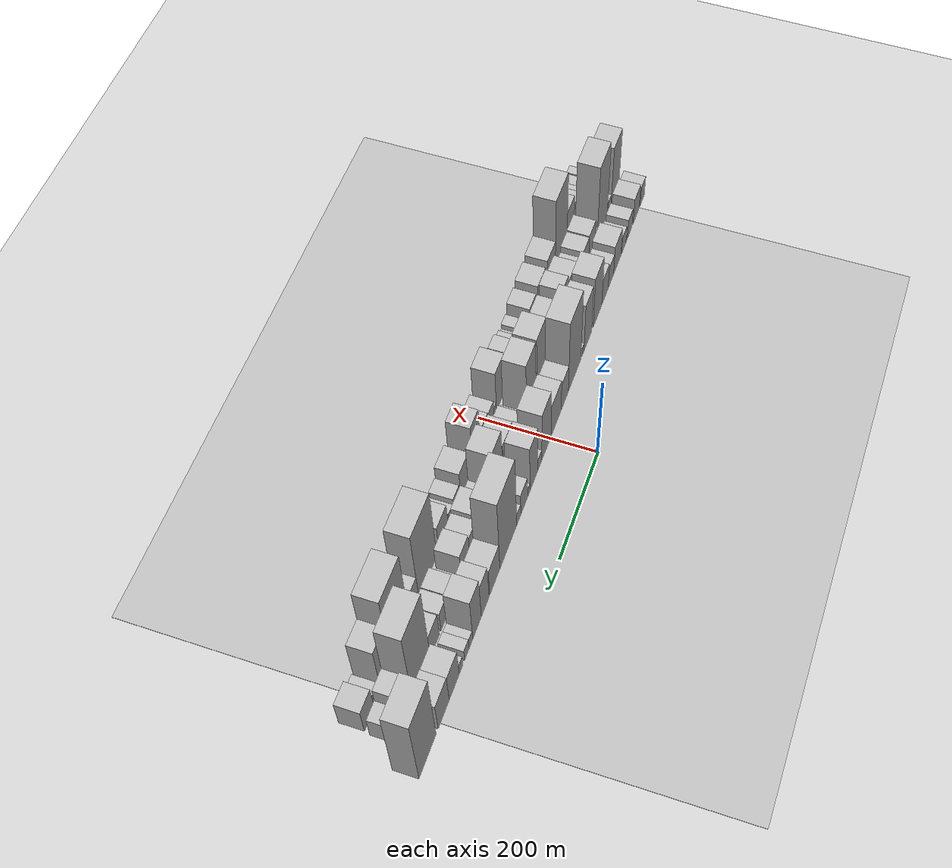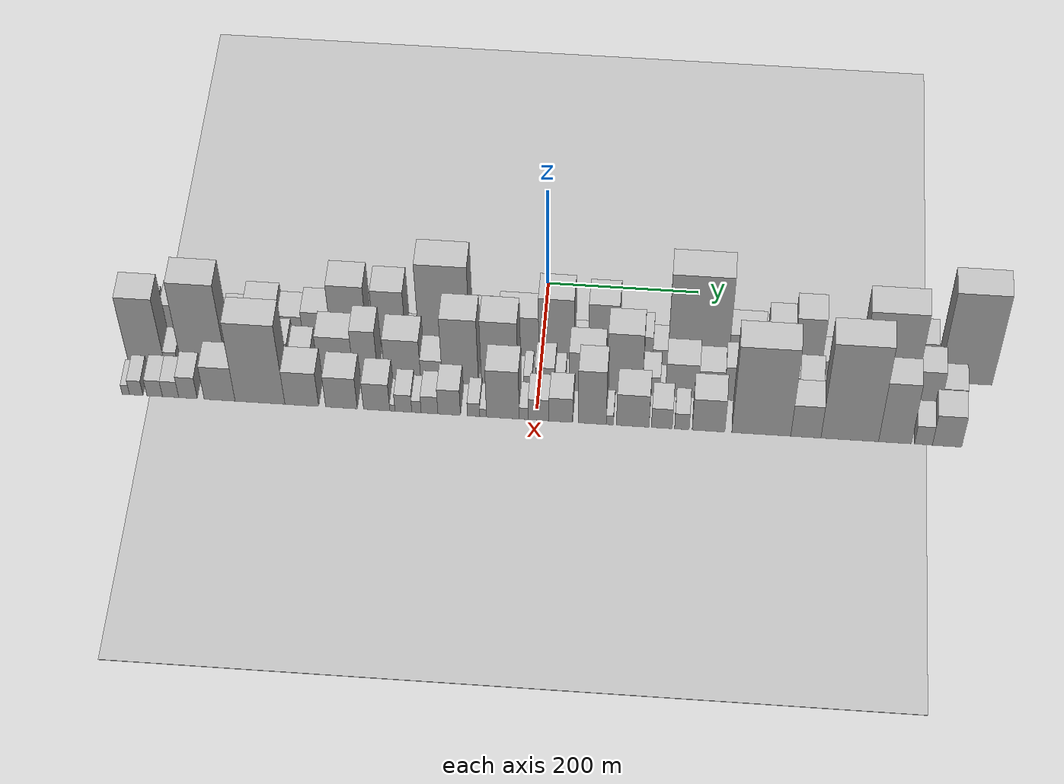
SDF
<?xml version="1.0" encoding="utf-8"?>

<sdf version="1.6">

   <world name="default">

      <gui fullscreen="0">

         <camera name="user_camera">

            <pose>-15 0 4.57585 0 0 0</pose>

            <view_controller>orbit</view_controller>

         </camera>

      </gui>

      <scene>

         <sky>

           <clouds>

             <speed>12</speed>

           </clouds>

         </sky>

         <ambient>0.4 0.4 0.4 1</ambient>

         <background>0.7 0.7 0.7 1</background>

         <shadows>1</shadows>

      </scene>

      <gravity>0 0 -9.8066</gravity>

      <magnetic_field>6e-06 2.3e-05 -4.2e-05</magnetic_field>

      <physics default="0" name="default_physics" type="ode">

         <ode>

            <solver>

               <type>quick</type>

               <iters>10</iters>

               <sor>1.0</sor>

               <use_dynamic_moi_rescaling>0</use_dynamic_moi_rescaling>

            </solver>

            <constraints>

               <cfm>0</cfm>

               <erp>0.2</erp>

               <contact_max_correcting_vel>100</contact_max_correcting_vel>

               <contact_surface_layer>0.001</contact_surface_layer>

            </constraints>

         </ode>

         <max_step_size>0.004</max_step_size>

         <real_time_factor>1</real_time_factor>

         <real_time_update_rate>250</real_time_update_rate>

      </physics>

      <light name="sun" type="directional">

         <cast_shadows>1</cast_shadows>

         <pose>0 0 10 0 0 0</pose>

         <diffuse>0.8 0.8 0.8 1</diffuse>

         <specular>0.2 0.2 0.2 1</specular>

         <attenuation>

            <range>1000</range>

            <constant>0.9</constant>

            <linear>0.01</linear>

            <quadratic>0.001</quadratic>

         </attenuation>

         <direction>-0.5 0.1 -0.9</direction>

      </light>

      <include>

         <name>ground_plane_1</name>

         <uri>model://HANNAS_ground_plane</uri>

         <pose>0 0 0  0 0 0</pose>

      </include>

      <include>

         <name>ground_plane_2</name>

         <uri>model://HANNAS_ground_plane</uri>

         <pose>100 0 0  0 0 0</pose>

      </include>

      <model name="building_1">

         <static>1</static>

         <pose frame="">100.0000 -515.4191 0 0.000000 0.000000 0.000000</pose>

         <link name="link">

            <pose frame="">0 0 25.50 0 0 0</pose>

            <collision name="collision">

               <geometry>

                  <box>

                     <size>40.0000 27.1618 51.0000</size>

                  </box>

               </geometry>

               <max_contacts>10</max_contacts>

               <surface>

                  <contact>

                     <ode/>

                  </contact>

                  <bounce/>

                  <friction>

                     <torsional>

                        <ode/>

                     </torsional>

                     <ode/>

                  </friction>

               </surface>

            </collision>

            <visual name="visual">

               <cast_shadows>0</cast_shadows>

               <geometry>

                  <box>

                     <size>40.0000 27.1618 51.0000</size>

                  </box>

               </geometry>

               <material>

                  <script>

                     <uri>model://HANNAS_wall/materials/scripts</uri>

                     <uri>model://HANNAS_wall/materials/textures</uri>

                     <name>vrc/HANNAS_wall</name>

                  </script>

               </material>

            </visual>

            <self_collide>0</self_collide>

            <enable_wind>0</enable_wind>

            <kinematic>0</kinematic>

         </link>

      </model>

      <model name="building_2">

         <static>1</static>

         <pose frame="">100.0000 -477.9174 0 0.000000 0.000000 0.000000</pose>

         <link name="link">

            <pose frame="">0 0 33.00 0 0 0</pose>

            <collision name="collision">

               <geometry>

                  <box>

                     <size>40.0000 35.8415 66.0000</size>

                  </box>

               </geometry>

               <max_contacts>10</max_contacts>

               <surface>

                  <contact>

                     <ode/>

                  </contact>

                  <bounce/>

                  <friction>

                     <torsional>

                        <ode/>

                     </torsional>

                     <ode/>

                  </friction>

               </surface>

            </collision>

            <visual name="visual">

               <cast_shadows>0</cast_shadows>

               <geometry>

                  <box>

                     <size>40.0000 35.8415 66.0000</size>

                  </box>

               </geometry>

               <material>

                  <script>

                     <uri>model://HANNAS_wall/materials/scripts</uri>

                     <uri>model://HANNAS_wall/materials/textures</uri>

                     <name>vrc/HANNAS_wall</name>

                  </script>

               </material>

            </visual>

            <self_collide>0</self_collide>

            <enable_wind>0</enable_wind>

            <kinematic>0</kinematic>

         </link>

      </model>

      <model name="building_3">

         <static>1</static>

         <pose frame="">100.0000 -438.5953 0 0.000000 0.000000 0.000000</pose>

         <link name="link">

            <pose frame="">0 0 25.50 0 0 0</pose>

            <collision name="collision">

               <geometry>

                  <box>

                     <size>40.0000 26.8026 51.0000</size>

                  </box>

               </geometry>

               <max_contacts>10</max_contacts>

               <surface>

                  <contact>

                     <ode/>

                  </contact>

                  <bounce/>

                  <friction>

                     <torsional>

                        <ode/>

                     </torsional>

                     <ode/>

                  </friction>

               </surface>

            </collision>

            <visual name="visual">

               <cast_shadows>0</cast_shadows>

               <geometry>

                  <box>

                     <size>40.0000 26.8026 51.0000</size>

                  </box>

               </geometry>

               <material>

                  <script>

                     <uri>model://HANNAS_wall/materials/scripts</uri>

                     <uri>model://HANNAS_wall/materials/textures</uri>

                     <name>vrc/HANNAS_wall</name>

                  </script>

               </material>

            </visual>

            <self_collide>0</self_collide>

            <enable_wind>0</enable_wind>

            <kinematic>0</kinematic>

         </link>

      </model>

      <model name="building_4">

         <static>1</static>

         <pose frame="">100.0000 -420.7293 0 0.000000 0.000000 0.000000</pose>

         <link name="link">

            <pose frame="">0 0 9.00 0 0 0</pose>

            <collision name="collision">

               <geometry>

                  <box>

                     <size>40.0000 8.9295 18.0000</size>

                  </box>

               </geometry>

               <max_contacts>10</max_contacts>

               <surface>

                  <contact>

                     <ode/>

                  </contact>

                  <bounce/>

                  <friction>

                     <torsional>

                        <ode/>

                     </torsional>

                     <ode/>

                  </friction>

               </surface>

            </collision>

            <visual name="visual">

               <cast_shadows>0</cast_shadows>

               <geometry>

                  <box>

                     <size>40.0000 8.9295 18.0000</size>

                  </box>

               </geometry>

               <material>

                  <script>

                     <uri>model://HANNAS_wall/materials/scripts</uri>

                     <uri>model://HANNAS_wall/materials/textures</uri>

                     <name>vrc/HANNAS_wall</name>

                  </script>

               </material>

            </visual>

            <self_collide>0</self_collide>

            <enable_wind>0</enable_wind>

            <kinematic>0</kinematic>

         </link>

      </model>

      <model name="building_5">

         <static>1</static>

         <pose frame="">100.0000 -403.0497 0 0.000000 0.000000 0.000000</pose>

         <link name="link">

            <pose frame="">0 0 22.50 0 0 0</pose>

            <collision name="collision">

               <geometry>

                  <box>

                     <size>40.0000 26.4296 45.0000</size>

                  </box>

               </geometry>

               <max_contacts>10</max_contacts>

               <surface>

                  <contact>

                     <ode/>

                  </contact>

                  <bounce/>

                  <friction>

                     <torsional>

                        <ode/>

                     </torsional>

                     <ode/>

                  </friction>

               </surface>

            </collision>

            <visual name="visual">

               <cast_shadows>0</cast_shadows>

               <geometry>

                  <box>

                     <size>40.0000 26.4296 45.0000</size>

                  </box>

               </geometry>

               <material>

                  <script>

                     <uri>model://HANNAS_wall/materials/scripts</uri>

                     <uri>model://HANNAS_wall/materials/textures</uri>

                     <name>vrc/HANNAS_wall</name>

                  </script>

               </material>

            </visual>

            <self_collide>0</self_collide>

            <enable_wind>0</enable_wind>

            <kinematic>0</kinematic>

         </link>

      </model>

      <model name="building_6">

         <static>1</static>

         <pose frame="">100.0000 -365.2503 0 0.000000 0.000000 0.000000</pose>

         <link name="link">

            <pose frame="">0 0 37.50 0 0 0</pose>

            <collision name="collision">

               <geometry>

                  <box>

                     <size>40.0000 43.1693 75.0000</size>

                  </box>

               </geometry>

               <max_contacts>10</max_contacts>

               <surface>

                  <contact>

                     <ode/>

                  </contact>

                  <bounce/>

                  <friction>

                     <torsional>

                        <ode/>

                     </torsional>

                     <ode/>

                  </friction>

               </surface>

            </collision>

            <visual name="visual">

               <cast_shadows>0</cast_shadows>

               <geometry>

                  <box>

                     <size>40.0000 43.1693 75.0000</size>

                  </box>

               </geometry>

               <material>

                  <script>

                     <uri>model://HANNAS_wall/materials/scripts</uri>

                     <uri>model://HANNAS_wall/materials/textures</uri>

                     <name>vrc/HANNAS_wall</name>

                  </script>

               </material>

            </visual>

            <self_collide>0</self_collide>

            <enable_wind>0</enable_wind>

            <kinematic>0</kinematic>

         </link>

      </model>

      <model name="building_7">

         <static>1</static>

         <pose frame="">100.0000 -327.9551 0 0.000000 0.000000 0.000000</pose>

         <link name="link">

            <pose frame="">0 0 28.50 0 0 0</pose>

            <collision name="collision">

               <geometry>

                  <box>

                     <size>40.0000 31.4211 57.0000</size>

                  </box>

               </geometry>

               <max_contacts>10</max_contacts>

               <surface>

                  <contact>

                     <ode/>

                  </contact>

                  <bounce/>

                  <friction>

                     <torsional>

                        <ode/>

                     </torsional>

                     <ode/>

                  </friction>

               </surface>

            </collision>

            <visual name="visual">

               <cast_shadows>0</cast_shadows>

               <geometry>

                  <box>

                     <size>40.0000 31.4211 57.0000</size>

                  </box>

               </geometry>

               <material>

                  <script>

                     <uri>model://HANNAS_wall/materials/scripts</uri>

                     <uri>model://HANNAS_wall/materials/textures</uri>

                     <name>vrc/HANNAS_wall</name>

                  </script>

               </material>

            </visual>

            <self_collide>0</self_collide>

            <enable_wind>0</enable_wind>

            <kinematic>0</kinematic>

         </link>

      </model>

      <model name="building_8">

         <static>1</static>

         <pose frame="">100.0000 -293.7208 0 0.000000 0.000000 0.000000</pose>

         <link name="link">

            <pose frame="">0 0 34.50 0 0 0</pose>

            <collision name="collision">

               <geometry>

                  <box>

                     <size>40.0000 37.0474 69.0000</size>

                  </box>

               </geometry>

               <max_contacts>10</max_contacts>

               <surface>

                  <contact>

                     <ode/>

                  </contact>

                  <bounce/>

                  <friction>

                     <torsional>

                        <ode/>

                     </torsional>

                     <ode/>

                  </friction>

               </surface>

            </collision>

            <visual name="visual">

               <cast_shadows>0</cast_shadows>

               <geometry>

                  <box>

                     <size>40.0000 37.0474 69.0000</size>

                  </box>

               </geometry>

               <material>

                  <script>

                     <uri>model://HANNAS_wall/materials/scripts</uri>

                     <uri>model://HANNAS_wall/materials/textures</uri>

                     <name>vrc/HANNAS_wall</name>

                  </script>

               </material>

            </visual>

            <self_collide>0</self_collide>

            <enable_wind>0</enable_wind>

            <kinematic>0</kinematic>

         </link>

      </model>

      <model name="building_9">

         <static>1</static>

         <pose frame="">100.0000 -251.4896 0 0.000000 0.000000 0.000000</pose>

         <link name="link">

            <pose frame="">0 0 66.00 0 0 0</pose>

            <collision name="collision">

               <geometry>

                  <box>

                     <size>40.0000 47.4151 132.0000</size>

                  </box>

               </geometry>

               <max_contacts>10</max_contacts>

               <surface>

                  <contact>

                     <ode/>

                  </contact>

                  <bounce/>

                  <friction>

                     <torsional>

                        <ode/>

                     </torsional>

                     <ode/>

                  </friction>

               </surface>

            </collision>

            <visual name="visual">

               <cast_shadows>0</cast_shadows>

               <geometry>

                  <box>

                     <size>40.0000 47.4151 132.0000</size>

                  </box>

               </geometry>

               <material>

                  <script>

                     <uri>model://HANNAS_wall/materials/scripts</uri>

                     <uri>model://HANNAS_wall/materials/textures</uri>

                     <name>vrc/HANNAS_wall</name>

                  </script>

               </material>

            </visual>

            <self_collide>0</self_collide>

            <enable_wind>0</enable_wind>

            <kinematic>0</kinematic>

         </link>

      </model>

      <model name="building_10">

         <static>1</static>

         <pose frame="">100.0000 -197.9140 0 0.000000 0.000000 0.000000</pose>

         <link name="link">

            <pose frame="">0 0 63.00 0 0 0</pose>

            <collision name="collision">

               <geometry>

                  <box>

                     <size>40.0000 41.7361 126.0000</size>

                  </box>

               </geometry>

               <max_contacts>10</max_contacts>

               <surface>

                  <contact>

                     <ode/>

                  </contact>

                  <bounce/>

                  <friction>

                     <torsional>

                        <ode/>

                     </torsional>

                     <ode/>

                  </friction>

               </surface>

            </collision>

            <visual name="visual">

               <cast_shadows>0</cast_shadows>

               <geometry>

                  <box>

                     <size>40.0000 41.7361 126.0000</size>

                  </box>

               </geometry>

               <material>

                  <script>

                     <uri>model://HANNAS_wall/materials/scripts</uri>

                     <uri>model://HANNAS_wall/materials/textures</uri>

                     <name>vrc/HANNAS_wall</name>

                  </script>

               </material>

            </visual>

            <self_collide>0</self_collide>

            <enable_wind>0</enable_wind>

            <kinematic>0</kinematic>

         </link>

      </model>

      <model name="building_11">

         <static>1</static>

         <pose frame="">100.0000 -171.9435 0 0.000000 0.000000 0.000000</pose>

         <link name="link">

            <pose frame="">0 0 12.00 0 0 0</pose>

            <collision name="collision">

               <geometry>

                  <box>

                     <size>40.0000 10.2050 24.0000</size>

                  </box>

               </geometry>

               <max_contacts>10</max_contacts>

               <surface>

                  <contact>

                     <ode/>

                  </contact>

                  <bounce/>

                  <friction>

                     <torsional>

                        <ode/>

                     </torsional>

                     <ode/>

                  </friction>

               </surface>

            </collision>

            <visual name="visual">

               <cast_shadows>0</cast_shadows>

               <geometry>

                  <box>

                     <size>40.0000 10.2050 24.0000</size>

                  </box>

               </geometry>

               <material>

                  <script>

                     <uri>model://HANNAS_wall/materials/scripts</uri>

                     <uri>model://HANNAS_wall/materials/textures</uri>

                     <name>vrc/HANNAS_wall</name>

                  </script>

               </material>

            </visual>

            <self_collide>0</self_collide>

            <enable_wind>0</enable_wind>

            <kinematic>0</kinematic>

         </link>

      </model>

      <model name="building_12">

         <static>1</static>

         <pose frame="">100.0000 -126.4781 0 0.000000 0.000000 0.000000</pose>

         <link name="link">

            <pose frame="">0 0 94.50 0 0 0</pose>

            <collision name="collision">

               <geometry>

                  <box>

                     <size>40.0000 66.7257 189.0000</size>

                  </box>

               </geometry>

               <max_contacts>10</max_contacts>

               <surface>

                  <contact>

                     <ode/>

                  </contact>

                  <bounce/>

                  <friction>

                     <torsional>

                        <ode/>

                     </torsional>

                     <ode/>

                  </friction>

               </surface>

            </collision>

            <visual name="visual">

               <cast_shadows>0</cast_shadows>

               <geometry>

                  <box>

                     <size>40.0000 66.7257 189.0000</size>

                  </box>

               </geometry>

               <material>

                  <script>

                     <uri>model://HANNAS_wall/materials/scripts</uri>

                     <uri>model://HANNAS_wall/materials/textures</uri>

                     <name>vrc/HANNAS_wall</name>

                  </script>

               </material>

            </visual>

            <self_collide>0</self_collide>

            <enable_wind>0</enable_wind>

            <kinematic>0</kinematic>

         </link>

      </model>

      <model name="building_13">

         <static>1</static>

         <pose frame="">100.0000 -74.3532 0 0.000000 0.000000 0.000000</pose>

         <link name="link">

            <pose frame="">0 0 37.50 0 0 0</pose>

            <collision name="collision">

               <geometry>

                  <box>

                     <size>40.0000 37.5241 75.0000</size>

                  </box>

               </geometry>

               <max_contacts>10</max_contacts>

               <surface>

                  <contact>

                     <ode/>

                  </contact>

                  <bounce/>

                  <friction>

                     <torsional>

                        <ode/>

                     </torsional>

                     <ode/>

                  </friction>

               </surface>

            </collision>

            <visual name="visual">

               <cast_shadows>0</cast_shadows>

               <geometry>

                  <box>

                     <size>40.0000 37.5241 75.0000</size>

                  </box>

               </geometry>

               <material>

                  <script>

                     <uri>model://HANNAS_wall/materials/scripts</uri>

                     <uri>model://HANNAS_wall/materials/textures</uri>

                     <name>vrc/HANNAS_wall</name>

                  </script>

               </material>

            </visual>

            <self_collide>0</self_collide>

            <enable_wind>0</enable_wind>

            <kinematic>0</kinematic>

         </link>

      </model>

      <model name="building_14">

         <static>1</static>

         <pose frame="">100.0000 -29.5392 0 0.000000 0.000000 0.000000</pose>

         <link name="link">

            <pose frame="">0 0 43.50 0 0 0</pose>

            <collision name="collision">

               <geometry>

                  <box>

                     <size>40.0000 52.1041 87.0000</size>

                  </box>

               </geometry>

               <max_contacts>10</max_contacts>

               <surface>

                  <contact>

                     <ode/>

                  </contact>

                  <bounce/>

                  <friction>

                     <torsional>

                        <ode/>

                     </torsional>

                     <ode/>

                  </friction>

               </surface>

            </collision>

            <visual name="visual">

               <cast_shadows>0</cast_shadows>

               <geometry>

                  <box>

                     <size>40.0000 52.1041 87.0000</size>

                  </box>

               </geometry>

               <material>

                  <script>

                     <uri>model://HANNAS_wall/materials/scripts</uri>

                     <uri>model://HANNAS_wall/materials/textures</uri>

                     <name>vrc/HANNAS_wall</name>

                  </script>

               </material>

            </visual>

            <self_collide>0</self_collide>

            <enable_wind>0</enable_wind>

            <kinematic>0</kinematic>

         </link>

      </model>

      <model name="building_15">

         <static>1</static>

         <pose frame="">100.0000 19.6133 0 0.000000 0.000000 0.000000</pose>

         <link name="link">

            <pose frame="">0 0 66.00 0 0 0</pose>

            <collision name="collision">

               <geometry>

                  <box>

                     <size>40.0000 46.2009 132.0000</size>

                  </box>

               </geometry>

               <max_contacts>10</max_contacts>

               <surface>

                  <contact>

                     <ode/>

                  </contact>

                  <bounce/>

                  <friction>

                     <torsional>

                        <ode/>

                     </torsional>

                     <ode/>

                  </friction>

               </surface>

            </collision>

            <visual name="visual">

               <cast_shadows>0</cast_shadows>

               <geometry>

                  <box>

                     <size>40.0000 46.2009 132.0000</size>

                  </box>

               </geometry>

               <material>

                  <script>

                     <uri>model://HANNAS_wall/materials/scripts</uri>

                     <uri>model://HANNAS_wall/materials/textures</uri>

                     <name>vrc/HANNAS_wall</name>

                  </script>

               </material>

            </visual>

            <self_collide>0</self_collide>

            <enable_wind>0</enable_wind>

            <kinematic>0</kinematic>

         </link>

      </model>

      <model name="building_16">

         <static>1</static>

         <pose frame="">100.0000 51.9696 0 0.000000 0.000000 0.000000</pose>

         <link name="link">

            <pose frame="">0 0 16.50 0 0 0</pose>

            <collision name="collision">

               <geometry>

                  <box>

                     <size>40.0000 18.5116 33.0000</size>

                  </box>

               </geometry>

               <max_contacts>10</max_contacts>

               <surface>

                  <contact>

                     <ode/>

                  </contact>

                  <bounce/>

                  <friction>

                     <torsional>

                        <ode/>

                     </torsional>

                     <ode/>

                  </friction>

               </surface>

            </collision>

            <visual name="visual">

               <cast_shadows>0</cast_shadows>

               <geometry>

                  <box>

                     <size>40.0000 18.5116 33.0000</size>

                  </box>

               </geometry>

               <material>

                  <script>

                     <uri>model://HANNAS_wall/materials/scripts</uri>

                     <uri>model://HANNAS_wall/materials/textures</uri>

                     <name>vrc/HANNAS_wall</name>

                  </script>

               </material>

            </visual>

            <self_collide>0</self_collide>

            <enable_wind>0</enable_wind>

            <kinematic>0</kinematic>

         </link>

      </model>

      <model name="building_17">

         <static>1</static>

         <pose frame="">100.0000 80.9882 0 0.000000 0.000000 0.000000</pose>

         <link name="link">

            <pose frame="">0 0 63.00 0 0 0</pose>

            <collision name="collision">

               <geometry>

                  <box>

                     <size>40.0000 39.5256 126.0000</size>

                  </box>

               </geometry>

               <max_contacts>10</max_contacts>

               <surface>

                  <contact>

                     <ode/>

                  </contact>

                  <bounce/>

                  <friction>

                     <torsional>

                        <ode/>

                     </torsional>

                     <ode/>

                  </friction>

               </surface>

            </collision>

            <visual name="visual">

               <cast_shadows>0</cast_shadows>

               <geometry>

                  <box>

                     <size>40.0000 39.5256 126.0000</size>

                  </box>

               </geometry>

               <material>

                  <script>

                     <uri>model://HANNAS_wall/materials/scripts</uri>

                     <uri>model://HANNAS_wall/materials/textures</uri>

                     <name>vrc/HANNAS_wall</name>

                  </script>

               </material>

            </visual>

            <self_collide>0</self_collide>

            <enable_wind>0</enable_wind>

            <kinematic>0</kinematic>

         </link>

      </model>

      <model name="building_18">

         <static>1</static>

         <pose frame="">100.0000 106.6039 0 0.000000 0.000000 0.000000</pose>

         <link name="link">

            <pose frame="">0 0 12.00 0 0 0</pose>

            <collision name="collision">

               <geometry>

                  <box>

                     <size>40.0000 11.7060 24.0000</size>

                  </box>

               </geometry>

               <max_contacts>10</max_contacts>

               <surface>

                  <contact>

                     <ode/>

                  </contact>

                  <bounce/>

                  <friction>

                     <torsional>

                        <ode/>

                     </torsional>

                     <ode/>

                  </friction>

               </surface>

            </collision>

            <visual name="visual">

               <cast_shadows>0</cast_shadows>

               <geometry>

                  <box>

                     <size>40.0000 11.7060 24.0000</size>

                  </box>

               </geometry>

               <material>

                  <script>

                     <uri>model://HANNAS_wall/materials/scripts</uri>

                     <uri>model://HANNAS_wall/materials/textures</uri>

                     <name>vrc/HANNAS_wall</name>

                  </script>

               </material>

            </visual>

            <self_collide>0</self_collide>

            <enable_wind>0</enable_wind>

            <kinematic>0</kinematic>

         </link>

      </model>

      <model name="building_19">

         <static>1</static>

         <pose frame="">100.0000 128.7293 0 0.000000 0.000000 0.000000</pose>

         <link name="link">

            <pose frame="">0 0 30.00 0 0 0</pose>

            <collision name="collision">

               <geometry>

                  <box>

                     <size>40.0000 32.5449 60.0000</size>

                  </box>

               </geometry>

               <max_contacts>10</max_contacts>

               <surface>

                  <contact>

                     <ode/>

                  </contact>

                  <bounce/>

                  <friction>

                     <torsional>

                        <ode/>

                     </torsional>

                     <ode/>

                  </friction>

               </surface>

            </collision>

            <visual name="visual">

               <cast_shadows>0</cast_shadows>

               <geometry>

                  <box>

                     <size>40.0000 32.5449 60.0000</size>

                  </box>

               </geometry>

               <material>

                  <script>

                     <uri>model://HANNAS_wall/materials/scripts</uri>

                     <uri>model://HANNAS_wall/materials/textures</uri>

                     <name>vrc/HANNAS_wall</name>

                  </script>

               </material>

            </visual>

            <self_collide>0</self_collide>

            <enable_wind>0</enable_wind>

            <kinematic>0</kinematic>

         </link>

      </model>

      <model name="building_20">

         <static>1</static>

         <pose frame="">100.0000 154.8038 0 0.000000 0.000000 0.000000</pose>

         <link name="link">

            <pose frame="">0 0 16.50 0 0 0</pose>

            <collision name="collision">

               <geometry>

                  <box>

                     <size>40.0000 19.6040 33.0000</size>

                  </box>

               </geometry>

               <max_contacts>10</max_contacts>

               <surface>

                  <contact>

                     <ode/>

                  </contact>

                  <bounce/>

                  <friction>

                     <torsional>

                        <ode/>

                     </torsional>

                     <ode/>

                  </friction>

               </surface>

            </collision>

            <visual name="visual">

               <cast_shadows>0</cast_shadows>

               <geometry>

                  <box>

                     <size>40.0000 19.6040 33.0000</size>

                  </box>

               </geometry>

               <material>

                  <script>

                     <uri>model://HANNAS_wall/materials/scripts</uri>

                     <uri>model://HANNAS_wall/materials/textures</uri>

                     <name>vrc/HANNAS_wall</name>

                  </script>

               </material>

            </visual>

            <self_collide>0</self_collide>

            <enable_wind>0</enable_wind>

            <kinematic>0</kinematic>

         </link>

      </model>

      <model name="building_21">

         <static>1</static>

         <pose frame="">100.0000 203.8623 0 0.000000 0.000000 0.000000</pose>

         <link name="link">

            <pose frame="">0 0 100.50 0 0 0</pose>

            <collision name="collision">

               <geometry>

                  <box>

                     <size>40.0000 78.5130 201.0000</size>

                  </box>

               </geometry>

               <max_contacts>10</max_contacts>

               <surface>

                  <contact>

                     <ode/>

                  </contact>

                  <bounce/>

                  <friction>

                     <torsional>

                        <ode/>

                     </torsional>

                     <ode/>

                  </friction>

               </surface>

            </collision>

            <visual name="visual">

               <cast_shadows>0</cast_shadows>

               <geometry>

                  <box>

                     <size>40.0000 78.5130 201.0000</size>

                  </box>

               </geometry>

               <material>

                  <script>

                     <uri>model://HANNAS_wall/materials/scripts</uri>

                     <uri>model://HANNAS_wall/materials/textures</uri>

                     <name>vrc/HANNAS_wall</name>

                  </script>

               </material>

            </visual>

            <self_collide>0</self_collide>

            <enable_wind>0</enable_wind>

            <kinematic>0</kinematic>

         </link>

      </model>

      <model name="building_22">

         <static>1</static>

         <pose frame="">100.0000 266.0745 0 0.000000 0.000000 0.000000</pose>

         <link name="link">

            <pose frame="">0 0 39.00 0 0 0</pose>

            <collision name="collision">

               <geometry>

                  <box>

                     <size>40.0000 45.9114 78.0000</size>

                  </box>

               </geometry>

               <max_contacts>10</max_contacts>

               <surface>

                  <contact>

                     <ode/>

                  </contact>

                  <bounce/>

                  <friction>

                     <torsional>

                        <ode/>

                     </torsional>

                     <ode/>

                  </friction>

               </surface>

            </collision>

            <visual name="visual">

               <cast_shadows>0</cast_shadows>

               <geometry>

                  <box>

                     <size>40.0000 45.9114 78.0000</size>

                  </box>

               </geometry>

               <material>

                  <script>

                     <uri>model://HANNAS_wall/materials/scripts</uri>

                     <uri>model://HANNAS_wall/materials/textures</uri>

                     <name>vrc/HANNAS_wall</name>

                  </script>

               </material>

            </visual>

            <self_collide>0</self_collide>

            <enable_wind>0</enable_wind>

            <kinematic>0</kinematic>

         </link>

      </model>

      <model name="building_23">

         <static>1</static>

         <pose frame="">100.0000 309.0728 0 0.000000 0.000000 0.000000</pose>

         <link name="link">

            <pose frame="">0 0 49.50 0 0 0</pose>

            <collision name="collision">

               <geometry>

                  <box>

                     <size>40.0000 34.0853 99.0000</size>

                  </box>

               </geometry>

               <max_contacts>10</max_contacts>

               <surface>

                  <contact>

                     <ode/>

                  </contact>

                  <bounce/>

                  <friction>

                     <torsional>

                        <ode/>

                     </torsional>

                     <ode/>

                  </friction>

               </surface>

            </collision>

            <visual name="visual">

               <cast_shadows>0</cast_shadows>

               <geometry>

                  <box>

                     <size>40.0000 34.0853 99.0000</size>

                  </box>

               </geometry>

               <material>

                  <script>

                     <uri>model://HANNAS_wall/materials/scripts</uri>

                     <uri>model://HANNAS_wall/materials/textures</uri>

                     <name>vrc/HANNAS_wall</name>

                  </script>

               </material>

            </visual>

            <self_collide>0</self_collide>

            <enable_wind>0</enable_wind>

            <kinematic>0</kinematic>

         </link>

      </model>

      <model name="building_24">

         <static>1</static>

         <pose frame="">100.0000 344.8599 0 0.000000 0.000000 0.000000</pose>

         <link name="link">

            <pose frame="">0 0 61.50 0 0 0</pose>

            <collision name="collision">

               <geometry>

                  <box>

                     <size>40.0000 37.4889 123.0000</size>

                  </box>

               </geometry>

               <max_contacts>10</max_contacts>

               <surface>

                  <contact>

                     <ode/>

                  </contact>

                  <bounce/>

                  <friction>

                     <torsional>

                        <ode/>

                     </torsional>

                     <ode/>

                  </friction>

               </surface>

            </collision>

            <visual name="visual">

               <cast_shadows>0</cast_shadows>

               <geometry>

                  <box>

                     <size>40.0000 37.4889 123.0000</size>

                  </box>

               </geometry>

               <material>

                  <script>

                     <uri>model://HANNAS_wall/materials/scripts</uri>

                     <uri>model://HANNAS_wall/materials/textures</uri>

                     <name>vrc/HANNAS_wall</name>

                  </script>

               </material>

            </visual>

            <self_collide>0</self_collide>

            <enable_wind>0</enable_wind>

            <kinematic>0</kinematic>

         </link>

      </model>

      <model name="building_25">

         <static>1</static>

         <pose frame="">100.0000 371.3807 0 0.000000 0.000000 0.000000</pose>

         <link name="link">

            <pose frame="">0 0 15.00 0 0 0</pose>

            <collision name="collision">

               <geometry>

                  <box>

                     <size>40.0000 15.5526 30.0000</size>

                  </box>

               </geometry>

               <max_contacts>10</max_contacts>

               <surface>

                  <contact>

                     <ode/>

                  </contact>

                  <bounce/>

                  <friction>

                     <torsional>

                        <ode/>

                     </torsional>

                     <ode/>

                  </friction>

               </surface>

            </collision>

            <visual name="visual">

               <cast_shadows>0</cast_shadows>

               <geometry>

                  <box>

                     <size>40.0000 15.5526 30.0000</size>

                  </box>

               </geometry>

               <material>

                  <script>

                     <uri>model://HANNAS_wall/materials/scripts</uri>

                     <uri>model://HANNAS_wall/materials/textures</uri>

                     <name>vrc/HANNAS_wall</name>

                  </script>

               </material>

            </visual>

            <self_collide>0</self_collide>

            <enable_wind>0</enable_wind>

            <kinematic>0</kinematic>

         </link>

      </model>

      <model name="building_26">

         <static>1</static>

         <pose frame="">100.0000 389.0259 0 0.000000 0.000000 0.000000</pose>

         <link name="link">

            <pose frame="">0 0 16.50 0 0 0</pose>

            <collision name="collision">

               <geometry>

                  <box>

                     <size>40.0000 19.7379 33.0000</size>

                  </box>

               </geometry>

               <max_contacts>10</max_contacts>

               <surface>

                  <contact>

                     <ode/>

                  </contact>

                  <bounce/>

                  <friction>

                     <torsional>

                        <ode/>

                     </torsional>

                     <ode/>

                  </friction>

               </surface>

            </collision>

            <visual name="visual">

               <cast_shadows>0</cast_shadows>

               <geometry>

                  <box>

                     <size>40.0000 19.7379 33.0000</size>

                  </box>

               </geometry>

               <material>

                  <script>

                     <uri>model://HANNAS_wall/materials/scripts</uri>

                     <uri>model://HANNAS_wall/materials/textures</uri>

                     <name>vrc/HANNAS_wall</name>

                  </script>

               </material>

            </visual>

            <self_collide>0</self_collide>

            <enable_wind>0</enable_wind>

            <kinematic>0</kinematic>

         </link>

      </model>

      <model name="building_27">

         <static>1</static>

         <pose frame="">100.0000 413.7134 0 0.000000 0.000000 0.000000</pose>

         <link name="link">

            <pose frame="">0 0 15.00 0 0 0</pose>

            <collision name="collision">

               <geometry>

                  <box>

                     <size>40.0000 15.6372 30.0000</size>

                  </box>

               </geometry>

               <max_contacts>10</max_contacts>

               <surface>

                  <contact>

                     <ode/>

                  </contact>

                  <bounce/>

                  <friction>

                     <torsional>

                        <ode/>

                     </torsional>

                     <ode/>

                  </friction>

               </surface>

            </collision>

            <visual name="visual">

               <cast_shadows>0</cast_shadows>

               <geometry>

                  <box>

                     <size>40.0000 15.6372 30.0000</size>

                  </box>

               </geometry>

               <material>

                  <script>

                     <uri>model://HANNAS_wall/materials/scripts</uri>

                     <uri>model://HANNAS_wall/materials/textures</uri>

                     <name>vrc/HANNAS_wall</name>

                  </script>

               </material>

            </visual>

            <self_collide>0</self_collide>

            <enable_wind>0</enable_wind>

            <kinematic>0</kinematic>

         </link>

      </model>

      <model name="building_28">

         <static>1</static>

         <pose frame="">100.0000 442.4184 0 0.000000 0.000000 0.000000</pose>

         <link name="link">

            <pose frame="">0 0 40.50 0 0 0</pose>

            <collision name="collision">

               <geometry>

                  <box>

                     <size>40.0000 41.7728 81.0000</size>

                  </box>

               </geometry>

               <max_contacts>10</max_contacts>

               <surface>

                  <contact>

                     <ode/>

                  </contact>

                  <bounce/>

                  <friction>

                     <torsional>

                        <ode/>

                     </torsional>

                     <ode/>

                  </friction>

               </surface>

            </collision>

            <visual name="visual">

               <cast_shadows>0</cast_shadows>

               <geometry>

                  <box>

                     <size>40.0000 41.7728 81.0000</size>

                  </box>

               </geometry>

               <material>

                  <script>

                     <uri>model://HANNAS_wall/materials/scripts</uri>

                     <uri>model://HANNAS_wall/materials/textures</uri>

                     <name>vrc/HANNAS_wall</name>

                  </script>

               </material>

            </visual>

            <self_collide>0</self_collide>

            <enable_wind>0</enable_wind>

            <kinematic>0</kinematic>

         </link>

      </model>

      <model name="building_29">

         <static>1</static>

         <pose frame="">100.0000 486.1446 0 0.000000 0.000000 0.000000</pose>

         <link name="link">

            <pose frame="">0 0 42.00 0 0 0</pose>

            <collision name="collision">

               <geometry>

                  <box>

                     <size>40.0000 45.6794 84.0000</size>

                  </box>

               </geometry>

               <max_contacts>10</max_contacts>

               <surface>

                  <contact>

                     <ode/>

                  </contact>

                  <bounce/>

                  <friction>

                     <torsional>

                        <ode/>

                     </torsional>

                     <ode/>

                  </friction>

               </surface>

            </collision>

            <visual name="visual">

               <cast_shadows>0</cast_shadows>

               <geometry>

                  <box>

                     <size>40.0000 45.6794 84.0000</size>

                  </box>

               </geometry>

               <material>

                  <script>

                     <uri>model://HANNAS_wall/materials/scripts</uri>

                     <uri>model://HANNAS_wall/materials/textures</uri>

                     <name>vrc/HANNAS_wall</name>

                  </script>

               </material>

            </visual>

            <self_collide>0</self_collide>

            <enable_wind>0</enable_wind>

            <kinematic>0</kinematic>

         </link>

      </model>

      <model name="building_30">

         <static>1</static>

         <pose frame="">100.0000 551.2728 0 0.000000 0.000000 0.000000</pose>

         <link name="link">

            <pose frame="">0 0 99.00 0 0 0</pose>

            <collision name="collision">

               <geometry>

                  <box>

                     <size>40.0000 68.5769 198.0000</size>

                  </box>

               </geometry>

               <max_contacts>10</max_contacts>

               <surface>

                  <contact>

                     <ode/>

                  </contact>

                  <bounce/>

                  <friction>

                     <torsional>

                        <ode/>

                     </torsional>

                     <ode/>

                  </friction>

               </surface>

            </collision>

            <visual name="visual">

               <cast_shadows>0</cast_shadows>

               <geometry>

                  <box>

                     <size>40.0000 68.5769 198.0000</size>

                  </box>

               </geometry>

               <material>

                  <script>

                     <uri>model://HANNAS_wall/materials/scripts</uri>

                     <uri>model://HANNAS_wall/materials/textures</uri>

                     <name>vrc/HANNAS_wall</name>

                  </script>

               </material>

            </visual>

            <self_collide>0</self_collide>

            <enable_wind>0</enable_wind>

            <kinematic>0</kinematic>

         </link>

      </model>

      <model name="building_31">

         <static>1</static>

         <pose frame="">149.0000 -512.1162 0 0.000000 0.000000 0.000000</pose>

         <link name="link">

            <pose frame="">0 0 73.50 0 0 0</pose>

            <collision name="collision">

               <geometry>

                  <box>

                     <size>40.0000 47.7676 147.0000</size>

                  </box>

               </geometry>

               <max_contacts>10</max_contacts>

               <surface>

                  <contact>

                     <ode/>

                  </contact>

                  <bounce/>

                  <friction>

                     <torsional>

                        <ode/>

                     </torsional>

                     <ode/>

                  </friction>

               </surface>

            </collision>

            <visual name="visual">

               <cast_shadows>0</cast_shadows>

               <geometry>

                  <box>

                     <size>40.0000 47.7676 147.0000</size>

                  </box>

               </geometry>

               <material>

                  <script>

                     <uri>model://HANNAS_wall/materials/scripts</uri>

                     <uri>model://HANNAS_wall/materials/textures</uri>

                     <name>vrc/HANNAS_wall</name>

                  </script>

               </material>

            </visual>

            <self_collide>0</self_collide>

            <enable_wind>0</enable_wind>

            <kinematic>0</kinematic>

         </link>

      </model>

      <model name="building_32">

         <static>1</static>

         <pose frame="">149.0000 -479.6060 0 0.000000 0.000000 0.000000</pose>

         <link name="link">

            <pose frame="">0 0 15.00 0 0 0</pose>

            <collision name="collision">

               <geometry>

                  <box>

                     <size>40.0000 17.2528 30.0000</size>

                  </box>

               </geometry>

               <max_contacts>10</max_contacts>

               <surface>

                  <contact>

                     <ode/>

                  </contact>

                  <bounce/>

                  <friction>

                     <torsional>

                        <ode/>

                     </torsional>

                     <ode/>

                  </friction>

               </surface>

            </collision>

            <visual name="visual">

               <cast_shadows>0</cast_shadows>

               <geometry>

                  <box>

                     <size>40.0000 17.2528 30.0000</size>

                  </box>

               </geometry>

               <material>

                  <script>

                     <uri>model://HANNAS_wall/materials/scripts</uri>

                     <uri>model://HANNAS_wall/materials/textures</uri>

                     <name>vrc/HANNAS_wall</name>

                  </script>

               </material>

            </visual>

            <self_collide>0</self_collide>

            <enable_wind>0</enable_wind>

            <kinematic>0</kinematic>

         </link>

      </model>

      <model name="building_33">

         <static>1</static>

         <pose frame="">149.0000 -436.1986 0 0.000000 0.000000 0.000000</pose>

         <link name="link">

            <pose frame="">0 0 93.00 0 0 0</pose>

            <collision name="collision">

               <geometry>

                  <box>

                     <size>40.0000 59.5618 186.0000</size>

                  </box>

               </geometry>

               <max_contacts>10</max_contacts>

               <surface>

                  <contact>

                     <ode/>

                  </contact>

                  <bounce/>

                  <friction>

                     <torsional>

                        <ode/>

                     </torsional>

                     <ode/>

                  </friction>

               </surface>

            </collision>

            <visual name="visual">

               <cast_shadows>0</cast_shadows>

               <geometry>

                  <box>

                     <size>40.0000 59.5618 186.0000</size>

                  </box>

               </geometry>

               <material>

                  <script>

                     <uri>model://HANNAS_wall/materials/scripts</uri>

                     <uri>model://HANNAS_wall/materials/textures</uri>

                     <name>vrc/HANNAS_wall</name>

                  </script>

               </material>

            </visual>

            <self_collide>0</self_collide>

            <enable_wind>0</enable_wind>

            <kinematic>0</kinematic>

         </link>

      </model>

      <model name="building_34">

         <static>1</static>

         <pose frame="">149.0000 -402.4930 0 0.000000 0.000000 0.000000</pose>

         <link name="link">

            <pose frame="">0 0 9.00 0 0 0</pose>

            <collision name="collision">

               <geometry>

                  <box>

                     <size>40.0000 7.8494 18.0000</size>

                  </box>

               </geometry>

               <max_contacts>10</max_contacts>

               <surface>

                  <contact>

                     <ode/>

                  </contact>

                  <bounce/>

                  <friction>

                     <torsional>

                        <ode/>

                     </torsional>

                     <ode/>

                  </friction>

               </surface>

            </collision>

            <visual name="visual">

               <cast_shadows>0</cast_shadows>

               <geometry>

                  <box>

                     <size>40.0000 7.8494 18.0000</size>

                  </box>

               </geometry>

               <material>

                  <script>

                     <uri>model://HANNAS_wall/materials/scripts</uri>

                     <uri>model://HANNAS_wall/materials/textures</uri>

                     <name>vrc/HANNAS_wall</name>

                  </script>

               </material>

            </visual>

            <self_collide>0</self_collide>

            <enable_wind>0</enable_wind>

            <kinematic>0</kinematic>

         </link>

      </model>

      <model name="building_35">

         <static>1</static>

         <pose frame="">149.0000 -375.4442 0 0.000000 0.000000 0.000000</pose>

         <link name="link">

            <pose frame="">0 0 34.50 0 0 0</pose>

            <collision name="collision">

               <geometry>

                  <box>

                     <size>40.0000 36.2482 69.0000</size>

                  </box>

               </geometry>

               <max_contacts>10</max_contacts>

               <surface>

                  <contact>

                     <ode/>

                  </contact>

                  <bounce/>

                  <friction>

                     <torsional>

                        <ode/>

                     </torsional>

                     <ode/>

                  </friction>

               </surface>

            </collision>

            <visual name="visual">

               <cast_shadows>0</cast_shadows>

               <geometry>

                  <box>

                     <size>40.0000 36.2482 69.0000</size>

                  </box>

               </geometry>

               <material>

                  <script>

                     <uri>model://HANNAS_wall/materials/scripts</uri>

                     <uri>model://HANNAS_wall/materials/textures</uri>

                     <name>vrc/HANNAS_wall</name>

                  </script>

               </material>

            </visual>

            <self_collide>0</self_collide>

            <enable_wind>0</enable_wind>

            <kinematic>0</kinematic>

         </link>

      </model>

      <model name="building_36">

         <static>1</static>

         <pose frame="">149.0000 -340.3787 0 0.000000 0.000000 0.000000</pose>

         <link name="link">

            <pose frame="">0 0 33.00 0 0 0</pose>

            <collision name="collision">

               <geometry>

                  <box>

                     <size>40.0000 33.8828 66.0000</size>

                  </box>

               </geometry>

               <max_contacts>10</max_contacts>

               <surface>

                  <contact>

                     <ode/>

                  </contact>

                  <bounce/>

                  <friction>

                     <torsional>

                        <ode/>

                     </torsional>

                     <ode/>

                  </friction>

               </surface>

            </collision>

            <visual name="visual">

               <cast_shadows>0</cast_shadows>

               <geometry>

                  <box>

                     <size>40.0000 33.8828 66.0000</size>

                  </box>

               </geometry>

               <material>

                  <script>

                     <uri>model://HANNAS_wall/materials/scripts</uri>

                     <uri>model://HANNAS_wall/materials/textures</uri>

                     <name>vrc/HANNAS_wall</name>

                  </script>

               </material>

            </visual>

            <self_collide>0</self_collide>

            <enable_wind>0</enable_wind>

            <kinematic>0</kinematic>

         </link>

      </model>

      <model name="building_37">

         <static>1</static>

         <pose frame="">149.0000 -309.0420 0 0.000000 0.000000 0.000000</pose>

         <link name="link">

            <pose frame="">0 0 25.50 0 0 0</pose>

            <collision name="collision">

               <geometry>

                  <box>

                     <size>40.0000 28.7906 51.0000</size>

                  </box>

               </geometry>

               <max_contacts>10</max_contacts>

               <surface>

                  <contact>

                     <ode/>

                  </contact>

                  <bounce/>

                  <friction>

                     <torsional>

                        <ode/>

                     </torsional>

                     <ode/>

                  </friction>

               </surface>

            </collision>

            <visual name="visual">

               <cast_shadows>0</cast_shadows>

               <geometry>

                  <box>

                     <size>40.0000 28.7906 51.0000</size>

                  </box>

               </geometry>

               <material>

                  <script>

                     <uri>model://HANNAS_wall/materials/scripts</uri>

                     <uri>model://HANNAS_wall/materials/textures</uri>

                     <name>vrc/HANNAS_wall</name>

                  </script>

               </material>

            </visual>

            <self_collide>0</self_collide>

            <enable_wind>0</enable_wind>

            <kinematic>0</kinematic>

         </link>

      </model>

      <model name="building_38">

         <static>1</static>

         <pose frame="">149.0000 -263.7271 0 0.000000 0.000000 0.000000</pose>

         <link name="link">

            <pose frame="">0 0 43.50 0 0 0</pose>

            <collision name="collision">

               <geometry>

                  <box>

                     <size>40.0000 45.8391 87.0000</size>

                  </box>

               </geometry>

               <max_contacts>10</max_contacts>

               <surface>

                  <contact>

                     <ode/>

                  </contact>

                  <bounce/>

                  <friction>

                     <torsional>

                        <ode/>

                     </torsional>

                     <ode/>

                  </friction>

               </surface>

            </collision>

            <visual name="visual">

               <cast_shadows>0</cast_shadows>

               <geometry>

                  <box>

                     <size>40.0000 45.8391 87.0000</size>

                  </box>

               </geometry>

               <material>

                  <script>

                     <uri>model://HANNAS_wall/materials/scripts</uri>

                     <uri>model://HANNAS_wall/materials/textures</uri>

                     <name>vrc/HANNAS_wall</name>

                  </script>

               </material>

            </visual>

            <self_collide>0</self_collide>

            <enable_wind>0</enable_wind>

            <kinematic>0</kinematic>

         </link>

      </model>

      <model name="building_39">

         <static>1</static>

         <pose frame="">149.0000 -224.7799 0 0.000000 0.000000 0.000000</pose>

         <link name="link">

            <pose frame="">0 0 52.50 0 0 0</pose>

            <collision name="collision">

               <geometry>

                  <box>

                     <size>40.0000 32.0554 105.0000</size>

                  </box>

               </geometry>

               <max_contacts>10</max_contacts>

               <surface>

                  <contact>

                     <ode/>

                  </contact>

                  <bounce/>

                  <friction>

                     <torsional>

                        <ode/>

                     </torsional>

                     <ode/>

                  </friction>

               </surface>

            </collision>

            <visual name="visual">

               <cast_shadows>0</cast_shadows>

               <geometry>

                  <box>

                     <size>40.0000 32.0554 105.0000</size>

                  </box>

               </geometry>

               <material>

                  <script>

                     <uri>model://HANNAS_wall/materials/scripts</uri>

                     <uri>model://HANNAS_wall/materials/textures</uri>

                     <name>vrc/HANNAS_wall</name>

                  </script>

               </material>

            </visual>

            <self_collide>0</self_collide>

            <enable_wind>0</enable_wind>

            <kinematic>0</kinematic>

         </link>

      </model>

      <model name="building_40">

         <static>1</static>

         <pose frame="">149.0000 -176.3824 0 0.000000 0.000000 0.000000</pose>

         <link name="link">

            <pose frame="">0 0 45.00 0 0 0</pose>

            <collision name="collision">

               <geometry>

                  <box>

                     <size>40.0000 46.7395 90.0000</size>

                  </box>

               </geometry>

               <max_contacts>10</max_contacts>

               <surface>

                  <contact>

                     <ode/>

                  </contact>

                  <bounce/>

                  <friction>

                     <torsional>

                        <ode/>

                     </torsional>

                     <ode/>

                  </friction>

               </surface>

            </collision>

            <visual name="visual">

               <cast_shadows>0</cast_shadows>

               <geometry>

                  <box>

                     <size>40.0000 46.7395 90.0000</size>

                  </box>

               </geometry>

               <material>

                  <script>

                     <uri>model://HANNAS_wall/materials/scripts</uri>

                     <uri>model://HANNAS_wall/materials/textures</uri>

                     <name>vrc/HANNAS_wall</name>

                  </script>

               </material>

            </visual>

            <self_collide>0</self_collide>

            <enable_wind>0</enable_wind>

            <kinematic>0</kinematic>

         </link>

      </model>

      <model name="building_41">

         <static>1</static>

         <pose frame="">149.0000 -138.9929 0 0.000000 0.000000 0.000000</pose>

         <link name="link">

            <pose frame="">0 0 24.00 0 0 0</pose>

            <collision name="collision">

               <geometry>

                  <box>

                     <size>40.0000 28.0394 48.0000</size>

                  </box>

               </geometry>

               <max_contacts>10</max_contacts>

               <surface>

                  <contact>

                     <ode/>

                  </contact>

                  <bounce/>

                  <friction>

                     <torsional>

                        <ode/>

                     </torsional>

                     <ode/>

                  </friction>

               </surface>

            </collision>

            <visual name="visual">

               <cast_shadows>0</cast_shadows>

               <geometry>

                  <box>

                     <size>40.0000 28.0394 48.0000</size>

                  </box>

               </geometry>

               <material>

                  <script>

                     <uri>model://HANNAS_wall/materials/scripts</uri>

                     <uri>model://HANNAS_wall/materials/textures</uri>

                     <name>vrc/HANNAS_wall</name>

                  </script>

               </material>

            </visual>

            <self_collide>0</self_collide>

            <enable_wind>0</enable_wind>

            <kinematic>0</kinematic>

         </link>

      </model>

      <model name="building_42">

         <static>1</static>

         <pose frame="">149.0000 -101.4500 0 0.000000 0.000000 0.000000</pose>

         <link name="link">

            <pose frame="">0 0 72.00 0 0 0</pose>

            <collision name="collision">

               <geometry>

                  <box>

                     <size>40.0000 47.0464 144.0000</size>

                  </box>

               </geometry>

               <max_contacts>10</max_contacts>

               <surface>

                  <contact>

                     <ode/>

                  </contact>

                  <bounce/>

                  <friction>

                     <torsional>

                        <ode/>

                     </torsional>

                     <ode/>

                  </friction>

               </surface>

            </collision>

            <visual name="visual">

               <cast_shadows>0</cast_shadows>

               <geometry>

                  <box>

                     <size>40.0000 47.0464 144.0000</size>

                  </box>

               </geometry>

               <material>

                  <script>

                     <uri>model://HANNAS_wall/materials/scripts</uri>

                     <uri>model://HANNAS_wall/materials/textures</uri>

                     <name>vrc/HANNAS_wall</name>

                  </script>

               </material>

            </visual>

            <self_collide>0</self_collide>

            <enable_wind>0</enable_wind>

            <kinematic>0</kinematic>

         </link>

      </model>

      <model name="building_43">

         <static>1</static>

         <pose frame="">149.0000 -50.2322 0 0.000000 0.000000 0.000000</pose>

         <link name="link">

            <pose frame="">0 0 72.00 0 0 0</pose>

            <collision name="collision">

               <geometry>

                  <box>

                     <size>40.0000 47.3893 144.0000</size>

                  </box>

               </geometry>

               <max_contacts>10</max_contacts>

               <surface>

                  <contact>

                     <ode/>

                  </contact>

                  <bounce/>

                  <friction>

                     <torsional>

                        <ode/>

                     </torsional>

                     <ode/>

                  </friction>

               </surface>

            </collision>

            <visual name="visual">

               <cast_shadows>0</cast_shadows>

               <geometry>

                  <box>

                     <size>40.0000 47.3893 144.0000</size>

                  </box>

               </geometry>

               <material>

                  <script>

                     <uri>model://HANNAS_wall/materials/scripts</uri>

                     <uri>model://HANNAS_wall/materials/textures</uri>

                     <name>vrc/HANNAS_wall</name>

                  </script>

               </material>

            </visual>

            <self_collide>0</self_collide>

            <enable_wind>0</enable_wind>

            <kinematic>0</kinematic>

         </link>

      </model>

      <model name="building_44">

         <static>1</static>

         <pose frame="">149.0000 -14.0285 0 0.000000 0.000000 0.000000</pose>

         <link name="link">

            <pose frame="">0 0 13.50 0 0 0</pose>

            <collision name="collision">

               <geometry>

                  <box>

                     <size>40.0000 11.0180 27.0000</size>

                  </box>

               </geometry>

               <max_contacts>10</max_contacts>

               <surface>

                  <contact>

                     <ode/>

                  </contact>

                  <bounce/>

                  <friction>

                     <torsional>

                        <ode/>

                     </torsional>

                     <ode/>

                  </friction>

               </surface>

            </collision>

            <visual name="visual">

               <cast_shadows>0</cast_shadows>

               <geometry>

                  <box>

                     <size>40.0000 11.0180 27.0000</size>

                  </box>

               </geometry>

               <material>

                  <script>

                     <uri>model://HANNAS_wall/materials/scripts</uri>

                     <uri>model://HANNAS_wall/materials/textures</uri>

                     <name>vrc/HANNAS_wall</name>

                  </script>

               </material>

            </visual>

            <self_collide>0</self_collide>

            <enable_wind>0</enable_wind>

            <kinematic>0</kinematic>

         </link>

      </model>

      <model name="building_45">

         <static>1</static>

         <pose frame="">149.0000 8.3008 0 0.000000 0.000000 0.000000</pose>

         <link name="link">

            <pose frame="">0 0 24.00 0 0 0</pose>

            <collision name="collision">

               <geometry>

                  <box>

                     <size>40.0000 25.6407 48.0000</size>

                  </box>

               </geometry>

               <max_contacts>10</max_contacts>

               <surface>

                  <contact>

                     <ode/>

                  </contact>

                  <bounce/>

                  <friction>

                     <torsional>

                        <ode/>

                     </torsional>

                     <ode/>

                  </friction>

               </surface>

            </collision>

            <visual name="visual">

               <cast_shadows>0</cast_shadows>

               <geometry>

                  <box>

                     <size>40.0000 25.6407 48.0000</size>

                  </box>

               </geometry>

               <material>

                  <script>

                     <uri>model://HANNAS_wall/materials/scripts</uri>

                     <uri>model://HANNAS_wall/materials/textures</uri>

                     <name>vrc/HANNAS_wall</name>

                  </script>

               </material>

            </visual>

            <self_collide>0</self_collide>

            <enable_wind>0</enable_wind>

            <kinematic>0</kinematic>

         </link>

      </model>

      <model name="building_46">

         <static>1</static>

         <pose frame="">149.0000 27.7729 0 0.000000 0.000000 0.000000</pose>

         <link name="link">

            <pose frame="">0 0 13.50 0 0 0</pose>

            <collision name="collision">

               <geometry>

                  <box>

                     <size>40.0000 13.3035 27.0000</size>

                  </box>

               </geometry>

               <max_contacts>10</max_contacts>

               <surface>

                  <contact>

                     <ode/>

                  </contact>

                  <bounce/>

                  <friction>

                     <torsional>

                        <ode/>

                     </torsional>

                     <ode/>

                  </friction>

               </surface>

            </collision>

            <visual name="visual">

               <cast_shadows>0</cast_shadows>

               <geometry>

                  <box>

                     <size>40.0000 13.3035 27.0000</size>

                  </box>

               </geometry>

               <material>

                  <script>

                     <uri>model://HANNAS_wall/materials/scripts</uri>

                     <uri>model://HANNAS_wall/materials/textures</uri>

                     <name>vrc/HANNAS_wall</name>

                  </script>

               </material>

            </visual>

            <self_collide>0</self_collide>

            <enable_wind>0</enable_wind>

            <kinematic>0</kinematic>

         </link>

      </model>

      <model name="building_47">

         <static>1</static>

         <pose frame="">149.0000 62.6030 0 0.000000 0.000000 0.000000</pose>

         <link name="link">

            <pose frame="">0 0 43.50 0 0 0</pose>

            <collision name="collision">

               <geometry>

                  <box>

                     <size>40.0000 46.3568 87.0000</size>

                  </box>

               </geometry>

               <max_contacts>10</max_contacts>

               <surface>

                  <contact>

                     <ode/>

                  </contact>

                  <bounce/>

                  <friction>

                     <torsional>

                        <ode/>

                     </torsional>

                     <ode/>

                  </friction>

               </surface>

            </collision>

            <visual name="visual">

               <cast_shadows>0</cast_shadows>

               <geometry>

                  <box>

                     <size>40.0000 46.3568 87.0000</size>

                  </box>

               </geometry>

               <material>

                  <script>

                     <uri>model://HANNAS_wall/materials/scripts</uri>

                     <uri>model://HANNAS_wall/materials/textures</uri>

                     <name>vrc/HANNAS_wall</name>

                  </script>

               </material>

            </visual>

            <self_collide>0</self_collide>

            <enable_wind>0</enable_wind>

            <kinematic>0</kinematic>

         </link>

      </model>

      <model name="building_48">

         <static>1</static>

         <pose frame="">149.0000 111.6222 0 0.000000 0.000000 0.000000</pose>

         <link name="link">

            <pose frame="">0 0 67.50 0 0 0</pose>

            <collision name="collision">

               <geometry>

                  <box>

                     <size>40.0000 45.6815 135.0000</size>

                  </box>

               </geometry>

               <max_contacts>10</max_contacts>

               <surface>

                  <contact>

                     <ode/>

                  </contact>

                  <bounce/>

                  <friction>

                     <torsional>

                        <ode/>

                     </torsional>

                     <ode/>

                  </friction>

               </surface>

            </collision>

            <visual name="visual">

               <cast_shadows>0</cast_shadows>

               <geometry>

                  <box>

                     <size>40.0000 45.6815 135.0000</size>

                  </box>

               </geometry>

               <material>

                  <script>

                     <uri>model://HANNAS_wall/materials/scripts</uri>

                     <uri>model://HANNAS_wall/materials/textures</uri>

                     <name>vrc/HANNAS_wall</name>

                  </script>

               </material>

            </visual>

            <self_collide>0</self_collide>

            <enable_wind>0</enable_wind>

            <kinematic>0</kinematic>

         </link>

      </model>

      <model name="building_49">

         <static>1</static>

         <pose frame="">149.0000 145.8154 0 0.000000 0.000000 0.000000</pose>

         <link name="link">

            <pose frame="">0 0 21.00 0 0 0</pose>

            <collision name="collision">

               <geometry>

                  <box>

                     <size>40.0000 22.7050 42.0000</size>

                  </box>

               </geometry>

               <max_contacts>10</max_contacts>

               <surface>

                  <contact>

                     <ode/>

                  </contact>

                  <bounce/>

                  <friction>

                     <torsional>

                        <ode/>

                     </torsional>

                     <ode/>

                  </friction>

               </surface>

            </collision>

            <visual name="visual">

               <cast_shadows>0</cast_shadows>

               <geometry>

                  <box>

                     <size>40.0000 22.7050 42.0000</size>

                  </box>

               </geometry>

               <material>

                  <script>

                     <uri>model://HANNAS_wall/materials/scripts</uri>

                     <uri>model://HANNAS_wall/materials/textures</uri>

                     <name>vrc/HANNAS_wall</name>

                  </script>

               </material>

            </visual>

            <self_collide>0</self_collide>

            <enable_wind>0</enable_wind>

            <kinematic>0</kinematic>

         </link>

      </model>

      <model name="building_50">

         <static>1</static>

         <pose frame="">149.0000 185.4181 0 0.000000 0.000000 0.000000</pose>

         <link name="link">

            <pose frame="">0 0 37.50 0 0 0</pose>

            <collision name="collision">

               <geometry>

                  <box>

                     <size>40.0000 42.5003 75.0000</size>

                  </box>

               </geometry>

               <max_contacts>10</max_contacts>

               <surface>

                  <contact>

                     <ode/>

                  </contact>

                  <bounce/>

                  <friction>

                     <torsional>

                        <ode/>

                     </torsional>

                     <ode/>

                  </friction>

               </surface>

            </collision>

            <visual name="visual">

               <cast_shadows>0</cast_shadows>

               <geometry>

                  <box>

                     <size>40.0000 42.5003 75.0000</size>

                  </box>

               </geometry>

               <material>

                  <script>

                     <uri>model://HANNAS_wall/materials/scripts</uri>

                     <uri>model://HANNAS_wall/materials/textures</uri>

                     <name>vrc/HANNAS_wall</name>

                  </script>

               </material>

            </visual>

            <self_collide>0</self_collide>

            <enable_wind>0</enable_wind>

            <kinematic>0</kinematic>

         </link>

      </model>

      <model name="building_51">

         <static>1</static>

         <pose frame="">149.0000 223.2690 0 0.000000 0.000000 0.000000</pose>

         <link name="link">

            <pose frame="">0 0 31.50 0 0 0</pose>

            <collision name="collision">

               <geometry>

                  <box>

                     <size>40.0000 33.2016 63.0000</size>

                  </box>

               </geometry>

               <max_contacts>10</max_contacts>

               <surface>

                  <contact>

                     <ode/>

                  </contact>

                  <bounce/>

                  <friction>

                     <torsional>

                        <ode/>

                     </torsional>

                     <ode/>

                  </friction>

               </surface>

            </collision>

            <visual name="visual">

               <cast_shadows>0</cast_shadows>

               <geometry>

                  <box>

                     <size>40.0000 33.2016 63.0000</size>

                  </box>

               </geometry>

               <material>

                  <script>

                     <uri>model://HANNAS_wall/materials/scripts</uri>

                     <uri>model://HANNAS_wall/materials/textures</uri>

                     <name>vrc/HANNAS_wall</name>

                  </script>

               </material>

            </visual>

            <self_collide>0</self_collide>

            <enable_wind>0</enable_wind>

            <kinematic>0</kinematic>

         </link>

      </model>

      <model name="building_52">

         <static>1</static>

         <pose frame="">149.0000 259.0389 0 0.000000 0.000000 0.000000</pose>

         <link name="link">

            <pose frame="">0 0 37.50 0 0 0</pose>

            <collision name="collision">

               <geometry>

                  <box>

                     <size>40.0000 38.3381 75.0000</size>

                  </box>

               </geometry>

               <max_contacts>10</max_contacts>

               <surface>

                  <contact>

                     <ode/>

                  </contact>

                  <bounce/>

                  <friction>

                     <torsional>

                        <ode/>

                     </torsional>

                     <ode/>

                  </friction>

               </surface>

            </collision>

            <visual name="visual">

               <cast_shadows>0</cast_shadows>

               <geometry>

                  <box>

                     <size>40.0000 38.3381 75.0000</size>

                  </box>

               </geometry>

               <material>

                  <script>

                     <uri>model://HANNAS_wall/materials/scripts</uri>

                     <uri>model://HANNAS_wall/materials/textures</uri>

                     <name>vrc/HANNAS_wall</name>

                  </script>

               </material>

            </visual>

            <self_collide>0</self_collide>

            <enable_wind>0</enable_wind>

            <kinematic>0</kinematic>

         </link>

      </model>

      <model name="building_53">

         <static>1</static>

         <pose frame="">149.0000 281.8146 0 0.000000 0.000000 0.000000</pose>

         <link name="link">

            <pose frame="">0 0 7.50 0 0 0</pose>

            <collision name="collision">

               <geometry>

                  <box>

                     <size>40.0000 7.2133 15.0000</size>

                  </box>

               </geometry>

               <max_contacts>10</max_contacts>

               <surface>

                  <contact>

                     <ode/>

                  </contact>

                  <bounce/>

                  <friction>

                     <torsional>

                        <ode/>

                     </torsional>

                     <ode/>

                  </friction>

               </surface>

            </collision>

            <visual name="visual">

               <cast_shadows>0</cast_shadows>

               <geometry>

                  <box>

                     <size>40.0000 7.2133 15.0000</size>

                  </box>

               </geometry>

               <material>

                  <script>

                     <uri>model://HANNAS_wall/materials/scripts</uri>

                     <uri>model://HANNAS_wall/materials/textures</uri>

                     <name>vrc/HANNAS_wall</name>

                  </script>

               </material>

            </visual>

            <self_collide>0</self_collide>

            <enable_wind>0</enable_wind>

            <kinematic>0</kinematic>

         </link>

      </model>

      <model name="building_54">

         <static>1</static>

         <pose frame="">149.0000 290.1175 0 0.000000 0.000000 0.000000</pose>

         <link name="link">

            <pose frame="">0 0 10.50 0 0 0</pose>

            <collision name="collision">

               <geometry>

                  <box>

                     <size>40.0000 9.3926 21.0000</size>

                  </box>

               </geometry>

               <max_contacts>10</max_contacts>

               <surface>

                  <contact>

                     <ode/>

                  </contact>

                  <bounce/>

                  <friction>

                     <torsional>

                        <ode/>

                     </torsional>

                     <ode/>

                  </friction>

               </surface>

            </collision>

            <visual name="visual">

               <cast_shadows>0</cast_shadows>

               <geometry>

                  <box>

                     <size>40.0000 9.3926 21.0000</size>

                  </box>

               </geometry>

               <material>

                  <script>

                     <uri>model://HANNAS_wall/materials/scripts</uri>

                     <uri>model://HANNAS_wall/materials/textures</uri>

                     <name>vrc/HANNAS_wall</name>

                  </script>

               </material>

            </visual>

            <self_collide>0</self_collide>

            <enable_wind>0</enable_wind>

            <kinematic>0</kinematic>

         </link>

      </model>

      <model name="building_55">

         <static>1</static>

         <pose frame="">149.0000 317.8023 0 0.000000 0.000000 0.000000</pose>

         <link name="link">

            <pose frame="">0 0 30.00 0 0 0</pose>

            <collision name="collision">

               <geometry>

                  <box>

                     <size>40.0000 33.9770 60.0000</size>

                  </box>

               </geometry>

               <max_contacts>10</max_contacts>

               <surface>

                  <contact>

                     <ode/>

                  </contact>

                  <bounce/>

                  <friction>

                     <torsional>

                        <ode/>

                     </torsional>

                     <ode/>

                  </friction>

               </surface>

            </collision>

            <visual name="visual">

               <cast_shadows>0</cast_shadows>

               <geometry>

                  <box>

                     <size>40.0000 33.9770 60.0000</size>

                  </box>

               </geometry>

               <material>

                  <script>

                     <uri>model://HANNAS_wall/materials/scripts</uri>

                     <uri>model://HANNAS_wall/materials/textures</uri>

                     <name>vrc/HANNAS_wall</name>

                  </script>

               </material>

            </visual>

            <self_collide>0</self_collide>

            <enable_wind>0</enable_wind>

            <kinematic>0</kinematic>

         </link>

      </model>

      <model name="building_56">

         <static>1</static>

         <pose frame="">149.0000 350.3615 0 0.000000 0.000000 0.000000</pose>

         <link name="link">

            <pose frame="">0 0 28.50 0 0 0</pose>

            <collision name="collision">

               <geometry>

                  <box>

                     <size>40.0000 31.1414 57.0000</size>

                  </box>

               </geometry>

               <max_contacts>10</max_contacts>

               <surface>

                  <contact>

                     <ode/>

                  </contact>

                  <bounce/>

                  <friction>

                     <torsional>

                        <ode/>

                     </torsional>

                     <ode/>

                  </friction>

               </surface>

            </collision>

            <visual name="visual">

               <cast_shadows>0</cast_shadows>

               <geometry>

                  <box>

                     <size>40.0000 31.1414 57.0000</size>

                  </box>

               </geometry>

               <material>

                  <script>

                     <uri>model://HANNAS_wall/materials/scripts</uri>

                     <uri>model://HANNAS_wall/materials/textures</uri>

                     <name>vrc/HANNAS_wall</name>

                  </script>

               </material>

            </visual>

            <self_collide>0</self_collide>

            <enable_wind>0</enable_wind>

            <kinematic>0</kinematic>

         </link>

      </model>

      <model name="building_57">

         <static>1</static>

         <pose frame="">149.0000 390.8647 0 0.000000 0.000000 0.000000</pose>

         <link name="link">

            <pose frame="">0 0 34.50 0 0 0</pose>

            <collision name="collision">

               <geometry>

                  <box>

                     <size>40.0000 37.8648 69.0000</size>

                  </box>

               </geometry>

               <max_contacts>10</max_contacts>

               <surface>

                  <contact>

                     <ode/>

                  </contact>

                  <bounce/>

                  <friction>

                     <torsional>

                        <ode/>

                     </torsional>

                     <ode/>

                  </friction>

               </surface>

            </collision>

            <visual name="visual">

               <cast_shadows>0</cast_shadows>

               <geometry>

                  <box>

                     <size>40.0000 37.8648 69.0000</size>

                  </box>

               </geometry>

               <material>

                  <script>

                     <uri>model://HANNAS_wall/materials/scripts</uri>

                     <uri>model://HANNAS_wall/materials/textures</uri>

                     <name>vrc/HANNAS_wall</name>

                  </script>

               </material>

            </visual>

            <self_collide>0</self_collide>

            <enable_wind>0</enable_wind>

            <kinematic>0</kinematic>

         </link>

      </model>

      <model name="building_58">

         <static>1</static>

         <pose frame="">149.0000 445.7684 0 0.000000 0.000000 0.000000</pose>

         <link name="link">

            <pose frame="">0 0 108.00 0 0 0</pose>

            <collision name="collision">

               <geometry>

                  <box>

                     <size>40.0000 71.9426 216.0000</size>

                  </box>

               </geometry>

               <max_contacts>10</max_contacts>

               <surface>

                  <contact>

                     <ode/>

                  </contact>

                  <bounce/>

                  <friction>

                     <torsional>

                        <ode/>

                     </torsional>

                     <ode/>

                  </friction>

               </surface>

            </collision>

            <visual name="visual">

               <cast_shadows>0</cast_shadows>

               <geometry>

                  <box>

                     <size>40.0000 71.9426 216.0000</size>

                  </box>

               </geometry>

               <material>

                  <script>

                     <uri>model://HANNAS_wall/materials/scripts</uri>

                     <uri>model://HANNAS_wall/materials/textures</uri>

                     <name>vrc/HANNAS_wall</name>

                  </script>

               </material>

            </visual>

            <self_collide>0</self_collide>

            <enable_wind>0</enable_wind>

            <kinematic>0</kinematic>

         </link>

      </model>

      <model name="building_59">

         <static>1</static>

         <pose frame="">149.0000 499.3610 0 0.000000 0.000000 0.000000</pose>

         <link name="link">

            <pose frame="">0 0 46.50 0 0 0</pose>

            <collision name="collision">

               <geometry>

                  <box>

                     <size>40.0000 35.2428 93.0000</size>

                  </box>

               </geometry>

               <max_contacts>10</max_contacts>

               <surface>

                  <contact>

                     <ode/>

                  </contact>

                  <bounce/>

                  <friction>

                     <torsional>

                        <ode/>

                     </torsional>

                     <ode/>

                  </friction>

               </surface>

            </collision>

            <visual name="visual">

               <cast_shadows>0</cast_shadows>

               <geometry>

                  <box>

                     <size>40.0000 35.2428 93.0000</size>

                  </box>

               </geometry>

               <material>

                  <script>

                     <uri>model://HANNAS_wall/materials/scripts</uri>

                     <uri>model://HANNAS_wall/materials/textures</uri>

                     <name>vrc/HANNAS_wall</name>

                  </script>

               </material>

            </visual>

            <self_collide>0</self_collide>

            <enable_wind>0</enable_wind>

            <kinematic>0</kinematic>

         </link>

      </model>

      <model name="building_60">

         <static>1</static>

         <pose frame="">149.0000 532.4834 0 0.000000 0.000000 0.000000</pose>

         <link name="link">

            <pose frame="">0 0 28.50 0 0 0</pose>

            <collision name="collision">

               <geometry>

                  <box>

                     <size>40.0000 31.0020 57.0000</size>

                  </box>

               </geometry>

               <max_contacts>10</max_contacts>

               <surface>

                  <contact>

                     <ode/>

                  </contact>

                  <bounce/>

                  <friction>

                     <torsional>

                        <ode/>

                     </torsional>

                     <ode/>

                  </friction>

               </surface>

            </collision>

            <visual name="visual">

               <cast_shadows>0</cast_shadows>

               <geometry>

                  <box>

                     <size>40.0000 31.0020 57.0000</size>

                  </box>

               </geometry>

               <material>

                  <script>

                     <uri>model://HANNAS_wall/materials/scripts</uri>

                     <uri>model://HANNAS_wall/materials/textures</uri>

                     <name>vrc/HANNAS_wall</name>

                  </script>

               </material>

            </visual>

            <self_collide>0</self_collide>

            <enable_wind>0</enable_wind>

            <kinematic>0</kinematic>

         </link>

      </model>

      <model name="building_61">

         <static>1</static>

         <pose frame="">198.0000 -531.2364 0 0.000000 0.000000 0.000000</pose>

         <link name="link">

            <pose frame="">0 0 10.50 0 0 0</pose>

            <collision name="collision">

               <geometry>

                  <box>

                     <size>40.0000 9.5272 21.0000</size>

                  </box>

               </geometry>

               <max_contacts>10</max_contacts>

               <surface>

                  <contact>

                     <ode/>

                  </contact>

                  <bounce/>

                  <friction>

                     <torsional>

                        <ode/>

                     </torsional>

                     <ode/>

                  </friction>

               </surface>

            </collision>

            <visual name="visual">

               <cast_shadows>0</cast_shadows>

               <geometry>

                  <box>

                     <size>40.0000 9.5272 21.0000</size>

                  </box>

               </geometry>

               <material>

                  <script>

                     <uri>model://HANNAS_wall/materials/scripts</uri>

                     <uri>model://HANNAS_wall/materials/textures</uri>

                     <name>vrc/HANNAS_wall</name>

                  </script>

               </material>

            </visual>

            <self_collide>0</self_collide>

            <enable_wind>0</enable_wind>

            <kinematic>0</kinematic>

         </link>

      </model>

      <model name="building_62">

         <static>1</static>

         <pose frame="">198.0000 -517.5872 0 0.000000 0.000000 0.000000</pose>

         <link name="link">

            <pose frame="">0 0 16.50 0 0 0</pose>

            <collision name="collision">

               <geometry>

                  <box>

                     <size>40.0000 17.7712 33.0000</size>

                  </box>

               </geometry>

               <max_contacts>10</max_contacts>

               <surface>

                  <contact>

                     <ode/>

                  </contact>

                  <bounce/>

                  <friction>

                     <torsional>

                        <ode/>

                     </torsional>

                     <ode/>

                  </friction>

               </surface>

            </collision>

            <visual name="visual">

               <cast_shadows>0</cast_shadows>

               <geometry>

                  <box>

                     <size>40.0000 17.7712 33.0000</size>

                  </box>

               </geometry>

               <material>

                  <script>

                     <uri>model://HANNAS_wall/materials/scripts</uri>

                     <uri>model://HANNAS_wall/materials/textures</uri>

                     <name>vrc/HANNAS_wall</name>

                  </script>

               </material>

            </visual>

            <self_collide>0</self_collide>

            <enable_wind>0</enable_wind>

            <kinematic>0</kinematic>

         </link>

      </model>

      <model name="building_63">

         <static>1</static>

         <pose frame="">198.0000 -493.5431 0 0.000000 0.000000 0.000000</pose>

         <link name="link">

            <pose frame="">0 0 18.00 0 0 0</pose>

            <collision name="collision">

               <geometry>

                  <box>

                     <size>40.0000 20.3170 36.0000</size>

                  </box>

               </geometry>

               <max_contacts>10</max_contacts>

               <surface>

                  <contact>

                     <ode/>

                  </contact>

                  <bounce/>

                  <friction>

                     <torsional>

                        <ode/>

                     </torsional>

                     <ode/>

                  </friction>

               </surface>

            </collision>

            <visual name="visual">

               <cast_shadows>0</cast_shadows>

               <geometry>

                  <box>

                     <size>40.0000 20.3170 36.0000</size>

                  </box>

               </geometry>

               <material>

                  <script>

                     <uri>model://HANNAS_wall/materials/scripts</uri>

                     <uri>model://HANNAS_wall/materials/textures</uri>

                     <name>vrc/HANNAS_wall</name>

                  </script>

               </material>

            </visual>

            <self_collide>0</self_collide>

            <enable_wind>0</enable_wind>

            <kinematic>0</kinematic>

         </link>

      </model>

      <model name="building_64">

         <static>1</static>

         <pose frame="">198.0000 -472.8137 0 0.000000 0.000000 0.000000</pose>

         <link name="link">

            <pose frame="">0 0 18.00 0 0 0</pose>

            <collision name="collision">

               <geometry>

                  <box>

                     <size>40.0000 21.1417 36.0000</size>

                  </box>

               </geometry>

               <max_contacts>10</max_contacts>

               <surface>

                  <contact>

                     <ode/>

                  </contact>

                  <bounce/>

                  <friction>

                     <torsional>

                        <ode/>

                     </torsional>

                     <ode/>

                  </friction>

               </surface>

            </collision>

            <visual name="visual">

               <cast_shadows>0</cast_shadows>

               <geometry>

                  <box>

                     <size>40.0000 21.1417 36.0000</size>

                  </box>

               </geometry>

               <material>

                  <script>

                     <uri>model://HANNAS_wall/materials/scripts</uri>

                     <uri>model://HANNAS_wall/materials/textures</uri>

                     <name>vrc/HANNAS_wall</name>

                  </script>

               </material>

            </visual>

            <self_collide>0</self_collide>

            <enable_wind>0</enable_wind>

            <kinematic>0</kinematic>

         </link>

      </model>

      <model name="building_65">

         <static>1</static>

         <pose frame="">198.0000 -450.1372 0 0.000000 0.000000 0.000000</pose>

         <link name="link">

            <pose frame="">0 0 24.00 0 0 0</pose>

            <collision name="collision">

               <geometry>

                  <box>

                     <size>40.0000 24.2114 48.0000</size>

                  </box>

               </geometry>

               <max_contacts>10</max_contacts>

               <surface>

                  <contact>

                     <ode/>

                  </contact>

                  <bounce/>

                  <friction>

                     <torsional>

                        <ode/>

                     </torsional>

                     <ode/>

                  </friction>

               </surface>

            </collision>

            <visual name="visual">

               <cast_shadows>0</cast_shadows>

               <geometry>

                  <box>

                     <size>40.0000 24.2114 48.0000</size>

                  </box>

               </geometry>

               <material>

                  <script>

                     <uri>model://HANNAS_wall/materials/scripts</uri>

                     <uri>model://HANNAS_wall/materials/textures</uri>

                     <name>vrc/HANNAS_wall</name>

                  </script>

               </material>

            </visual>

            <self_collide>0</self_collide>

            <enable_wind>0</enable_wind>

            <kinematic>0</kinematic>

         </link>

      </model>

      <model name="building_66">

         <static>1</static>

         <pose frame="">198.0000 -408.8999 0 0.000000 0.000000 0.000000</pose>

         <link name="link">

            <pose frame="">0 0 37.50 0 0 0</pose>

            <collision name="collision">

               <geometry>

                  <box>

                     <size>40.0000 40.2631 75.0000</size>

                  </box>

               </geometry>

               <max_contacts>10</max_contacts>

               <surface>

                  <contact>

                     <ode/>

                  </contact>

                  <bounce/>

                  <friction>

                     <torsional>

                        <ode/>

                     </torsional>

                     <ode/>

                  </friction>

               </surface>

            </collision>

            <visual name="visual">

               <cast_shadows>0</cast_shadows>

               <geometry>

                  <box>

                     <size>40.0000 40.2631 75.0000</size>

                  </box>

               </geometry>

               <material>

                  <script>

                     <uri>model://HANNAS_wall/materials/scripts</uri>

                     <uri>model://HANNAS_wall/materials/textures</uri>

                     <name>vrc/HANNAS_wall</name>

                  </script>

               </material>

            </visual>

            <self_collide>0</self_collide>

            <enable_wind>0</enable_wind>

            <kinematic>0</kinematic>

         </link>

      </model>

      <model name="building_67">

         <static>1</static>

         <pose frame="">198.0000 -356.4191 0 0.000000 0.000000 0.000000</pose>

         <link name="link">

            <pose frame="">0 0 88.50 0 0 0</pose>

            <collision name="collision">

               <geometry>

                  <box>

                     <size>40.0000 64.6985 177.0000</size>

                  </box>

               </geometry>

               <max_contacts>10</max_contacts>

               <surface>

                  <contact>

                     <ode/>

                  </contact>

                  <bounce/>

                  <friction>

                     <torsional>

                        <ode/>

                     </torsional>

                     <ode/>

                  </friction>

               </surface>

            </collision>

            <visual name="visual">

               <cast_shadows>0</cast_shadows>

               <geometry>

                  <box>

                     <size>40.0000 64.6985 177.0000</size>

                  </box>

               </geometry>

               <material>

                  <script>

                     <uri>model://HANNAS_wall/materials/scripts</uri>

                     <uri>model://HANNAS_wall/materials/textures</uri>

                     <name>vrc/HANNAS_wall</name>

                  </script>

               </material>

            </visual>

            <self_collide>0</self_collide>

            <enable_wind>0</enable_wind>

            <kinematic>0</kinematic>

         </link>

      </model>

      <model name="building_68">

         <static>1</static>

         <pose frame="">198.0000 -302.1386 0 0.000000 0.000000 0.000000</pose>

         <link name="link">

            <pose frame="">0 0 37.50 0 0 0</pose>

            <collision name="collision">

               <geometry>

                  <box>

                     <size>40.0000 43.8625 75.0000</size>

                  </box>

               </geometry>

               <max_contacts>10</max_contacts>

               <surface>

                  <contact>

                     <ode/>

                  </contact>

                  <bounce/>

                  <friction>

                     <torsional>

                        <ode/>

                     </torsional>

                     <ode/>

                  </friction>

               </surface>

            </collision>

            <visual name="visual">

               <cast_shadows>0</cast_shadows>

               <geometry>

                  <box>

                     <size>40.0000 43.8625 75.0000</size>

                  </box>

               </geometry>

               <material>

                  <script>

                     <uri>model://HANNAS_wall/materials/scripts</uri>

                     <uri>model://HANNAS_wall/materials/textures</uri>

                     <name>vrc/HANNAS_wall</name>

                  </script>

               </material>

            </visual>

            <self_collide>0</self_collide>

            <enable_wind>0</enable_wind>

            <kinematic>0</kinematic>

         </link>

      </model>

      <model name="building_69">

         <static>1</static>

         <pose frame="">198.0000 -250.6526 0 0.000000 0.000000 0.000000</pose>

         <link name="link">

            <pose frame="">0 0 34.50 0 0 0</pose>

            <collision name="collision">

               <geometry>

                  <box>

                     <size>40.0000 41.1093 69.0000</size>

                  </box>

               </geometry>

               <max_contacts>10</max_contacts>

               <surface>

                  <contact>

                     <ode/>

                  </contact>

                  <bounce/>

                  <friction>

                     <torsional>

                        <ode/>

                     </torsional>

                     <ode/>

                  </friction>

               </surface>

            </collision>

            <visual name="visual">

               <cast_shadows>0</cast_shadows>

               <geometry>

                  <box>

                     <size>40.0000 41.1093 69.0000</size>

                  </box>

               </geometry>

               <material>

                  <script>

                     <uri>model://HANNAS_wall/materials/scripts</uri>

                     <uri>model://HANNAS_wall/materials/textures</uri>

                     <name>vrc/HANNAS_wall</name>

                  </script>

               </material>

            </visual>

            <self_collide>0</self_collide>

            <enable_wind>0</enable_wind>

            <kinematic>0</kinematic>

         </link>

      </model>

      <model name="building_70">

         <static>1</static>

         <pose frame="">198.0000 -205.0424 0 0.000000 0.000000 0.000000</pose>

         <link name="link">

            <pose frame="">0 0 30.00 0 0 0</pose>

            <collision name="collision">

               <geometry>

                  <box>

                     <size>40.0000 34.1110 60.0000</size>

                  </box>

               </geometry>

               <max_contacts>10</max_contacts>

               <surface>

                  <contact>

                     <ode/>

                  </contact>

                  <bounce/>

                  <friction>

                     <torsional>

                        <ode/>

                     </torsional>

                     <ode/>

                  </friction>

               </surface>

            </collision>

            <visual name="visual">

               <cast_shadows>0</cast_shadows>

               <geometry>

                  <box>

                     <size>40.0000 34.1110 60.0000</size>

                  </box>

               </geometry>

               <material>

                  <script>

                     <uri>model://HANNAS_wall/materials/scripts</uri>

                     <uri>model://HANNAS_wall/materials/textures</uri>

                     <name>vrc/HANNAS_wall</name>

                  </script>

               </material>

            </visual>

            <self_collide>0</self_collide>

            <enable_wind>0</enable_wind>

            <kinematic>0</kinematic>

         </link>

      </model>

      <model name="building_71">

         <static>1</static>

         <pose frame="">198.0000 -184.6856 0 0.000000 0.000000 0.000000</pose>

         <link name="link">

            <pose frame="">0 0 7.50 0 0 0</pose>

            <collision name="collision">

               <geometry>

                  <box>

                     <size>40.0000 6.6028 15.0000</size>

                  </box>

               </geometry>

               <max_contacts>10</max_contacts>

               <surface>

                  <contact>

                     <ode/>

                  </contact>

                  <bounce/>

                  <friction>

                     <torsional>

                        <ode/>

                     </torsional>

                     <ode/>

                  </friction>

               </surface>

            </collision>

            <visual name="visual">

               <cast_shadows>0</cast_shadows>

               <geometry>

                  <box>

                     <size>40.0000 6.6028 15.0000</size>

                  </box>

               </geometry>

               <material>

                  <script>

                     <uri>model://HANNAS_wall/materials/scripts</uri>

                     <uri>model://HANNAS_wall/materials/textures</uri>

                     <name>vrc/HANNAS_wall</name>

                  </script>

               </material>

            </visual>

            <self_collide>0</self_collide>

            <enable_wind>0</enable_wind>

            <kinematic>0</kinematic>

         </link>

      </model>

      <model name="building_72">

         <static>1</static>

         <pose frame="">198.0000 -170.5244 0 0.000000 0.000000 0.000000</pose>

         <link name="link">

            <pose frame="">0 0 19.50 0 0 0</pose>

            <collision name="collision">

               <geometry>

                  <box>

                     <size>40.0000 21.7196 39.0000</size>

                  </box>

               </geometry>

               <max_contacts>10</max_contacts>

               <surface>

                  <contact>

                     <ode/>

                  </contact>

                  <bounce/>

                  <friction>

                     <torsional>

                        <ode/>

                     </torsional>

                     <ode/>

                  </friction>

               </surface>

            </collision>

            <visual name="visual">

               <cast_shadows>0</cast_shadows>

               <geometry>

                  <box>

                     <size>40.0000 21.7196 39.0000</size>

                  </box>

               </geometry>

               <material>

                  <script>

                     <uri>model://HANNAS_wall/materials/scripts</uri>

                     <uri>model://HANNAS_wall/materials/textures</uri>

                     <name>vrc/HANNAS_wall</name>

                  </script>

               </material>

            </visual>

            <self_collide>0</self_collide>

            <enable_wind>0</enable_wind>

            <kinematic>0</kinematic>

         </link>

      </model>

      <model name="building_73">

         <static>1</static>

         <pose frame="">198.0000 -153.5845 0 0.000000 0.000000 0.000000</pose>

         <link name="link">

            <pose frame="">0 0 13.50 0 0 0</pose>

            <collision name="collision">

               <geometry>

                  <box>

                     <size>40.0000 12.1603 27.0000</size>

                  </box>

               </geometry>

               <max_contacts>10</max_contacts>

               <surface>

                  <contact>

                     <ode/>

                  </contact>

                  <bounce/>

                  <friction>

                     <torsional>

                        <ode/>

                     </torsional>

                     <ode/>

                  </friction>

               </surface>

            </collision>

            <visual name="visual">

               <cast_shadows>0</cast_shadows>

               <geometry>

                  <box>

                     <size>40.0000 12.1603 27.0000</size>

                  </box>

               </geometry>

               <material>

                  <script>

                     <uri>model://HANNAS_wall/materials/scripts</uri>

                     <uri>model://HANNAS_wall/materials/textures</uri>

                     <name>vrc/HANNAS_wall</name>

                  </script>

               </material>

            </visual>

            <self_collide>0</self_collide>

            <enable_wind>0</enable_wind>

            <kinematic>0</kinematic>

         </link>

      </model>

      <model name="building_74">

         <static>1</static>

         <pose frame="">198.0000 -136.6719 0 0.000000 0.000000 0.000000</pose>

         <link name="link">

            <pose frame="">0 0 19.50 0 0 0</pose>

            <collision name="collision">

               <geometry>

                  <box>

                     <size>40.0000 21.6650 39.0000</size>

                  </box>

               </geometry>

               <max_contacts>10</max_contacts>

               <surface>

                  <contact>

                     <ode/>

                  </contact>

                  <bounce/>

                  <friction>

                     <torsional>

                        <ode/>

                     </torsional>

                     <ode/>

                  </friction>

               </surface>

            </collision>

            <visual name="visual">

               <cast_shadows>0</cast_shadows>

               <geometry>

                  <box>

                     <size>40.0000 21.6650 39.0000</size>

                  </box>

               </geometry>

               <material>

                  <script>

                     <uri>model://HANNAS_wall/materials/scripts</uri>

                     <uri>model://HANNAS_wall/materials/textures</uri>

                     <name>vrc/HANNAS_wall</name>

                  </script>

               </material>

            </visual>

            <self_collide>0</self_collide>

            <enable_wind>0</enable_wind>

            <kinematic>0</kinematic>

         </link>

      </model>

      <model name="building_75">

         <static>1</static>

         <pose frame="">198.0000 -111.2808 0 0.000000 0.000000 0.000000</pose>

         <link name="link">

            <pose frame="">0 0 28.50 0 0 0</pose>

            <collision name="collision">

               <geometry>

                  <box>

                     <size>40.0000 29.1170 57.0000</size>

                  </box>

               </geometry>

               <max_contacts>10</max_contacts>

               <surface>

                  <contact>

                     <ode/>

                  </contact>

                  <bounce/>

                  <friction>

                     <torsional>

                        <ode/>

                     </torsional>

                     <ode/>

                  </friction>

               </surface>

            </collision>

            <visual name="visual">

               <cast_shadows>0</cast_shadows>

               <geometry>

                  <box>

                     <size>40.0000 29.1170 57.0000</size>

                  </box>

               </geometry>

               <material>

                  <script>

                     <uri>model://HANNAS_wall/materials/scripts</uri>

                     <uri>model://HANNAS_wall/materials/textures</uri>

                     <name>vrc/HANNAS_wall</name>

                  </script>

               </material>

            </visual>

            <self_collide>0</self_collide>

            <enable_wind>0</enable_wind>

            <kinematic>0</kinematic>

         </link>

      </model>

      <model name="building_76">

         <static>1</static>

         <pose frame="">198.0000 -79.7653 0 0.000000 0.000000 0.000000</pose>

         <link name="link">

            <pose frame="">0 0 15.00 0 0 0</pose>

            <collision name="collision">

               <geometry>

                  <box>

                     <size>40.0000 15.9142 30.0000</size>

                  </box>

               </geometry>

               <max_contacts>10</max_contacts>

               <surface>

                  <contact>

                     <ode/>

                  </contact>

                  <bounce/>

                  <friction>

                     <torsional>

                        <ode/>

                     </torsional>

                     <ode/>

                  </friction>

               </surface>

            </collision>

            <visual name="visual">

               <cast_shadows>0</cast_shadows>

               <geometry>

                  <box>

                     <size>40.0000 15.9142 30.0000</size>

                  </box>

               </geometry>

               <material>

                  <script>

                     <uri>model://HANNAS_wall/materials/scripts</uri>

                     <uri>model://HANNAS_wall/materials/textures</uri>

                     <name>vrc/HANNAS_wall</name>

                  </script>

               </material>

            </visual>

            <self_collide>0</self_collide>

            <enable_wind>0</enable_wind>

            <kinematic>0</kinematic>

         </link>

      </model>

      <model name="building_77">

         <static>1</static>

         <pose frame="">198.0000 -67.4274 0 0.000000 0.000000 0.000000</pose>

         <link name="link">

            <pose frame="">0 0 9.00 0 0 0</pose>

            <collision name="collision">

               <geometry>

                  <box>

                     <size>40.0000 8.7616 18.0000</size>

                  </box>

               </geometry>

               <max_contacts>10</max_contacts>

               <surface>

                  <contact>

                     <ode/>

                  </contact>

                  <bounce/>

                  <friction>

                     <torsional>

                        <ode/>

                     </torsional>

                     <ode/>

                  </friction>

               </surface>

            </collision>

            <visual name="visual">

               <cast_shadows>0</cast_shadows>

               <geometry>

                  <box>

                     <size>40.0000 8.7616 18.0000</size>

                  </box>

               </geometry>

               <material>

                  <script>

                     <uri>model://HANNAS_wall/materials/scripts</uri>

                     <uri>model://HANNAS_wall/materials/textures</uri>

                     <name>vrc/HANNAS_wall</name>

                  </script>

               </material>

            </visual>

            <self_collide>0</self_collide>

            <enable_wind>0</enable_wind>

            <kinematic>0</kinematic>

         </link>

      </model>

      <model name="building_78">

         <static>1</static>

         <pose frame="">198.0000 -41.9660 0 0.000000 0.000000 0.000000</pose>

         <link name="link">

            <pose frame="">0 0 54.00 0 0 0</pose>

            <collision name="collision">

               <geometry>

                  <box>

                     <size>40.0000 42.1612 108.0000</size>

                  </box>

               </geometry>

               <max_contacts>10</max_contacts>

               <surface>

                  <contact>

                     <ode/>

                  </contact>

                  <bounce/>

                  <friction>

                     <torsional>

                        <ode/>

                     </torsional>

                     <ode/>

                  </friction>

               </surface>

            </collision>

            <visual name="visual">

               <cast_shadows>0</cast_shadows>

               <geometry>

                  <box>

                     <size>40.0000 42.1612 108.0000</size>

                  </box>

               </geometry>

               <material>

                  <script>

                     <uri>model://HANNAS_wall/materials/scripts</uri>

                     <uri>model://HANNAS_wall/materials/textures</uri>

                     <name>vrc/HANNAS_wall</name>

                  </script>

               </material>

            </visual>

            <self_collide>0</self_collide>

            <enable_wind>0</enable_wind>

            <kinematic>0</kinematic>

         </link>

      </model>

      <model name="building_79">

         <static>1</static>

         <pose frame="">198.0000 -15.1527 0 0.000000 0.000000 0.000000</pose>

         <link name="link">

            <pose frame="">0 0 13.50 0 0 0</pose>

            <collision name="collision">

               <geometry>

                  <box>

                     <size>40.0000 11.4653 27.0000</size>

                  </box>

               </geometry>

               <max_contacts>10</max_contacts>

               <surface>

                  <contact>

                     <ode/>

                  </contact>

                  <bounce/>

                  <friction>

                     <torsional>

                        <ode/>

                     </torsional>

                     <ode/>

                  </friction>

               </surface>

            </collision>

            <visual name="visual">

               <cast_shadows>0</cast_shadows>

               <geometry>

                  <box>

                     <size>40.0000 11.4653 27.0000</size>

                  </box>

               </geometry>

               <material>

                  <script>

                     <uri>model://HANNAS_wall/materials/scripts</uri>

                     <uri>model://HANNAS_wall/materials/textures</uri>

                     <name>vrc/HANNAS_wall</name>

                  </script>

               </material>

            </visual>

            <self_collide>0</self_collide>

            <enable_wind>0</enable_wind>

            <kinematic>0</kinematic>

         </link>

      </model>

      <model name="building_80">

         <static>1</static>

         <pose frame="">198.0000 4.0115 0 0.000000 0.000000 0.000000</pose>

         <link name="link">

            <pose frame="">0 0 24.00 0 0 0</pose>

            <collision name="collision">

               <geometry>

                  <box>

                     <size>40.0000 26.8633 48.0000</size>

                  </box>

               </geometry>

               <max_contacts>10</max_contacts>

               <surface>

                  <contact>

                     <ode/>

                  </contact>

                  <bounce/>

                  <friction>

                     <torsional>

                        <ode/>

                     </torsional>

                     <ode/>

                  </friction>

               </surface>

            </collision>

            <visual name="visual">

               <cast_shadows>0</cast_shadows>

               <geometry>

                  <box>

                     <size>40.0000 26.8633 48.0000</size>

                  </box>

               </geometry>

               <material>

                  <script>

                     <uri>model://HANNAS_wall/materials/scripts</uri>

                     <uri>model://HANNAS_wall/materials/textures</uri>

                     <name>vrc/HANNAS_wall</name>

                  </script>

               </material>

            </visual>

            <self_collide>0</self_collide>

            <enable_wind>0</enable_wind>

            <kinematic>0</kinematic>

         </link>

      </model>

      <model name="building_81">

         <static>1</static>

         <pose frame="">198.0000 32.6216 0 0.000000 0.000000 0.000000</pose>

         <link name="link">

            <pose frame="">0 0 27.00 0 0 0</pose>

            <collision name="collision">

               <geometry>

                  <box>

                     <size>40.0000 30.3568 54.0000</size>

                  </box>

               </geometry>

               <max_contacts>10</max_contacts>

               <surface>

                  <contact>

                     <ode/>

                  </contact>

                  <bounce/>

                  <friction>

                     <torsional>

                        <ode/>

                     </torsional>

                     <ode/>

                  </friction>

               </surface>

            </collision>

            <visual name="visual">

               <cast_shadows>0</cast_shadows>

               <geometry>

                  <box>

                     <size>40.0000 30.3568 54.0000</size>

                  </box>

               </geometry>

               <material>

                  <script>

                     <uri>model://HANNAS_wall/materials/scripts</uri>

                     <uri>model://HANNAS_wall/materials/textures</uri>

                     <name>vrc/HANNAS_wall</name>

                  </script>

               </material>

            </visual>

            <self_collide>0</self_collide>

            <enable_wind>0</enable_wind>

            <kinematic>0</kinematic>

         </link>

      </model>

      <model name="building_82">

         <static>1</static>

         <pose frame="">198.0000 72.8680 0 0.000000 0.000000 0.000000</pose>

         <link name="link">

            <pose frame="">0 0 60.00 0 0 0</pose>

            <collision name="collision">

               <geometry>

                  <box>

                     <size>40.0000 36.1361 120.0000</size>

                  </box>

               </geometry>

               <max_contacts>10</max_contacts>

               <surface>

                  <contact>

                     <ode/>

                  </contact>

                  <bounce/>

                  <friction>

                     <torsional>

                        <ode/>

                     </torsional>

                     <ode/>

                  </friction>

               </surface>

            </collision>

            <visual name="visual">

               <cast_shadows>0</cast_shadows>

               <geometry>

                  <box>

                     <size>40.0000 36.1361 120.0000</size>

                  </box>

               </geometry>

               <material>

                  <script>

                     <uri>model://HANNAS_wall/materials/scripts</uri>

                     <uri>model://HANNAS_wall/materials/textures</uri>

                     <name>vrc/HANNAS_wall</name>

                  </script>

               </material>

            </visual>

            <self_collide>0</self_collide>

            <enable_wind>0</enable_wind>

            <kinematic>0</kinematic>

         </link>

      </model>

      <model name="building_83">

         <static>1</static>

         <pose frame="">198.0000 95.5000 0 0.000000 0.000000 0.000000</pose>

         <link name="link">

            <pose frame="">0 0 10.50 0 0 0</pose>

            <collision name="collision">

               <geometry>

                  <box>

                     <size>40.0000 9.1279 21.0000</size>

                  </box>

               </geometry>

               <max_contacts>10</max_contacts>

               <surface>

                  <contact>

                     <ode/>

                  </contact>

                  <bounce/>

                  <friction>

                     <torsional>

                        <ode/>

                     </torsional>

                     <ode/>

                  </friction>

               </surface>

            </collision>

            <visual name="visual">

               <cast_shadows>0</cast_shadows>

               <geometry>

                  <box>

                     <size>40.0000 9.1279 21.0000</size>

                  </box>

               </geometry>

               <material>

                  <script>

                     <uri>model://HANNAS_wall/materials/scripts</uri>

                     <uri>model://HANNAS_wall/materials/textures</uri>

                     <name>vrc/HANNAS_wall</name>

                  </script>

               </material>

            </visual>

            <self_collide>0</self_collide>

            <enable_wind>0</enable_wind>

            <kinematic>0</kinematic>

         </link>

      </model>

      <model name="building_84">

         <static>1</static>

         <pose frame="">198.0000 125.0189 0 0.000000 0.000000 0.000000</pose>

         <link name="link">

            <pose frame="">0 0 36.00 0 0 0</pose>

            <collision name="collision">

               <geometry>

                  <box>

                     <size>40.0000 41.9098 72.0000</size>

                  </box>

               </geometry>

               <max_contacts>10</max_contacts>

               <surface>

                  <contact>

                     <ode/>

                  </contact>

                  <bounce/>

                  <friction>

                     <torsional>

                        <ode/>

                     </torsional>

                     <ode/>

                  </friction>

               </surface>

            </collision>

            <visual name="visual">

               <cast_shadows>0</cast_shadows>

               <geometry>

                  <box>

                     <size>40.0000 41.9098 72.0000</size>

                  </box>

               </geometry>

               <material>

                  <script>

                     <uri>model://HANNAS_wall/materials/scripts</uri>

                     <uri>model://HANNAS_wall/materials/textures</uri>

                     <name>vrc/HANNAS_wall</name>

                  </script>

               </material>

            </visual>

            <self_collide>0</self_collide>

            <enable_wind>0</enable_wind>

            <kinematic>0</kinematic>

         </link>

      </model>

      <model name="building_85">

         <static>1</static>

         <pose frame="">198.0000 162.3603 0 0.000000 0.000000 0.000000</pose>

         <link name="link">

            <pose frame="">0 0 22.50 0 0 0</pose>

            <collision name="collision">

               <geometry>

                  <box>

                     <size>40.0000 26.7731 45.0000</size>

                  </box>

               </geometry>

               <max_contacts>10</max_contacts>

               <surface>

                  <contact>

                     <ode/>

                  </contact>

                  <bounce/>

                  <friction>

                     <torsional>

                        <ode/>

                     </torsional>

                     <ode/>

                  </friction>

               </surface>

            </collision>

            <visual name="visual">

               <cast_shadows>0</cast_shadows>

               <geometry>

                  <box>

                     <size>40.0000 26.7731 45.0000</size>

                  </box>

               </geometry>

               <material>

                  <script>

                     <uri>model://HANNAS_wall/materials/scripts</uri>

                     <uri>model://HANNAS_wall/materials/textures</uri>

                     <name>vrc/HANNAS_wall</name>

                  </script>

               </material>

            </visual>

            <self_collide>0</self_collide>

            <enable_wind>0</enable_wind>

            <kinematic>0</kinematic>

         </link>

      </model>

      <model name="building_86">

         <static>1</static>

         <pose frame="">198.0000 188.0313 0 0.000000 0.000000 0.000000</pose>

         <link name="link">

            <pose frame="">0 0 18.00 0 0 0</pose>

            <collision name="collision">

               <geometry>

                  <box>

                     <size>40.0000 18.5689 36.0000</size>

                  </box>

               </geometry>

               <max_contacts>10</max_contacts>

               <surface>

                  <contact>

                     <ode/>

                  </contact>

                  <bounce/>

                  <friction>

                     <torsional>

                        <ode/>

                     </torsional>

                     <ode/>

                  </friction>

               </surface>

            </collision>

            <visual name="visual">

               <cast_shadows>0</cast_shadows>

               <geometry>

                  <box>

                     <size>40.0000 18.5689 36.0000</size>

                  </box>

               </geometry>

               <material>

                  <script>

                     <uri>model://HANNAS_wall/materials/scripts</uri>

                     <uri>model://HANNAS_wall/materials/textures</uri>

                     <name>vrc/HANNAS_wall</name>

                  </script>

               </material>

            </visual>

            <self_collide>0</self_collide>

            <enable_wind>0</enable_wind>

            <kinematic>0</kinematic>

         </link>

      </model>

      <model name="building_87">

         <static>1</static>

         <pose frame="">198.0000 222.1833 0 0.000000 0.000000 0.000000</pose>

         <link name="link">

            <pose frame="">0 0 36.00 0 0 0</pose>

            <collision name="collision">

               <geometry>

                  <box>

                     <size>40.0000 41.7352 72.0000</size>

                  </box>

               </geometry>

               <max_contacts>10</max_contacts>

               <surface>

                  <contact>

                     <ode/>

                  </contact>

                  <bounce/>

                  <friction>

                     <torsional>

                        <ode/>

                     </torsional>

                     <ode/>

                  </friction>

               </surface>

            </collision>

            <visual name="visual">

               <cast_shadows>0</cast_shadows>

               <geometry>

                  <box>

                     <size>40.0000 41.7352 72.0000</size>

                  </box>

               </geometry>

               <material>

                  <script>

                     <uri>model://HANNAS_wall/materials/scripts</uri>

                     <uri>model://HANNAS_wall/materials/textures</uri>

                     <name>vrc/HANNAS_wall</name>

                  </script>

               </material>

            </visual>

            <self_collide>0</self_collide>

            <enable_wind>0</enable_wind>

            <kinematic>0</kinematic>

         </link>

      </model>

      <model name="building_88">

         <static>1</static>

         <pose frame="">198.0000 289.7257 0 0.000000 0.000000 0.000000</pose>

         <link name="link">

            <pose frame="">0 0 97.50 0 0 0</pose>

            <collision name="collision">

               <geometry>

                  <box>

                     <size>40.0000 75.3495 195.0000</size>

                  </box>

               </geometry>

               <max_contacts>10</max_contacts>

               <surface>

                  <contact>

                     <ode/>

                  </contact>

                  <bounce/>

                  <friction>

                     <torsional>

                        <ode/>

                     </torsional>

                     <ode/>

                  </friction>

               </surface>

            </collision>

            <visual name="visual">

               <cast_shadows>0</cast_shadows>

               <geometry>

                  <box>

                     <size>40.0000 75.3495 195.0000</size>

                  </box>

               </geometry>

               <material>

                  <script>

                     <uri>model://HANNAS_wall/materials/scripts</uri>

                     <uri>model://HANNAS_wall/materials/textures</uri>

                     <name>vrc/HANNAS_wall</name>

                  </script>

               </material>

            </visual>

            <self_collide>0</self_collide>

            <enable_wind>0</enable_wind>

            <kinematic>0</kinematic>

         </link>

      </model>

      <model name="building_89">

         <static>1</static>

         <pose frame="">198.0000 346.6404 0 0.000000 0.000000 0.000000</pose>

         <link name="link">

            <pose frame="">0 0 36.00 0 0 0</pose>

            <collision name="collision">

               <geometry>

                  <box>

                     <size>40.0000 38.4800 72.0000</size>

                  </box>

               </geometry>

               <max_contacts>10</max_contacts>

               <surface>

                  <contact>

                     <ode/>

                  </contact>

                  <bounce/>

                  <friction>

                     <torsional>

                        <ode/>

                     </torsional>

                     <ode/>

                  </friction>

               </surface>

            </collision>

            <visual name="visual">

               <cast_shadows>0</cast_shadows>

               <geometry>

                  <box>

                     <size>40.0000 38.4800 72.0000</size>

                  </box>

               </geometry>

               <material>

                  <script>

                     <uri>model://HANNAS_wall/materials/scripts</uri>

                     <uri>model://HANNAS_wall/materials/textures</uri>

                     <name>vrc/HANNAS_wall</name>

                  </script>

               </material>

            </visual>

            <self_collide>0</self_collide>

            <enable_wind>0</enable_wind>

            <kinematic>0</kinematic>

         </link>

      </model>

      <model name="building_90">

         <static>1</static>

         <pose frame="">198.0000 402.6195 0 0.000000 0.000000 0.000000</pose>

         <link name="link">

            <pose frame="">0 0 106.50 0 0 0</pose>

            <collision name="collision">

               <geometry>

                  <box>

                     <size>40.0000 73.4781 213.0000</size>

                  </box>

               </geometry>

               <max_contacts>10</max_contacts>

               <surface>

                  <contact>

                     <ode/>

                  </contact>

                  <bounce/>

                  <friction>

                     <torsional>

                        <ode/>

                     </torsional>

                     <ode/>

                  </friction>

               </surface>

            </collision>

            <visual name="visual">

               <cast_shadows>0</cast_shadows>

               <geometry>

                  <box>

                     <size>40.0000 73.4781 213.0000</size>

                  </box>

               </geometry>

               <material>

                  <script>

                     <uri>model://HANNAS_wall/materials/scripts</uri>

                     <uri>model://HANNAS_wall/materials/textures</uri>

                     <name>vrc/HANNAS_wall</name>

                  </script>

               </material>

            </visual>

            <self_collide>0</self_collide>

            <enable_wind>0</enable_wind>

            <kinematic>0</kinematic>

         </link>

      </model>

      <model name="building_91">

         <static>1</static>

         <pose frame="">198.0000 460.2468 0 0.000000 0.000000 0.000000</pose>

         <link name="link">

            <pose frame="">0 0 67.50 0 0 0</pose>

            <collision name="collision">

               <geometry>

                  <box>

                     <size>40.0000 41.7766 135.0000</size>

                  </box>

               </geometry>

               <max_contacts>10</max_contacts>

               <surface>

                  <contact>

                     <ode/>

                  </contact>

                  <bounce/>

                  <friction>

                     <torsional>

                        <ode/>

                     </torsional>

                     <ode/>

                  </friction>

               </surface>

            </collision>

            <visual name="visual">

               <cast_shadows>0</cast_shadows>

               <geometry>

                  <box>

                     <size>40.0000 41.7766 135.0000</size>

                  </box>

               </geometry>

               <material>

                  <script>

                     <uri>model://HANNAS_wall/materials/scripts</uri>

                     <uri>model://HANNAS_wall/materials/textures</uri>

                     <name>vrc/HANNAS_wall</name>

                  </script>

               </material>

            </visual>

            <self_collide>0</self_collide>

            <enable_wind>0</enable_wind>

            <kinematic>0</kinematic>

         </link>

      </model>

      <model name="building_92">

         <static>1</static>

         <pose frame="">198.0000 496.5347 0 0.000000 0.000000 0.000000</pose>

         <link name="link">

            <pose frame="">0 0 21.00 0 0 0</pose>

            <collision name="collision">

               <geometry>

                  <box>

                     <size>40.0000 22.7993 42.0000</size>

                  </box>

               </geometry>

               <max_contacts>10</max_contacts>

               <surface>

                  <contact>

                     <ode/>

                  </contact>

                  <bounce/>

                  <friction>

                     <torsional>

                        <ode/>

                     </torsional>

                     <ode/>

                  </friction>

               </surface>

            </collision>

            <visual name="visual">

               <cast_shadows>0</cast_shadows>

               <geometry>

                  <box>

                     <size>40.0000 22.7993 42.0000</size>

                  </box>

               </geometry>

               <material>

                  <script>

                     <uri>model://HANNAS_wall/materials/scripts</uri>

                     <uri>model://HANNAS_wall/materials/textures</uri>

                     <name>vrc/HANNAS_wall</name>

                  </script>

               </material>

            </visual>

            <self_collide>0</self_collide>

            <enable_wind>0</enable_wind>

            <kinematic>0</kinematic>

         </link>

      </model>

      <model name="building_93">

         <static>1</static>

         <pose frame="">198.0000 526.5574 0 0.000000 0.000000 0.000000</pose>

         <link name="link">

            <pose frame="">0 0 34.50 0 0 0</pose>

            <collision name="collision">

               <geometry>

                  <box>

                     <size>40.0000 37.2461 69.0000</size>

                  </box>

               </geometry>

               <max_contacts>10</max_contacts>

               <surface>

                  <contact>

                     <ode/>

                  </contact>

                  <bounce/>

                  <friction>

                     <torsional>

                        <ode/>

                     </torsional>

                     <ode/>

                  </friction>

               </surface>

            </collision>

            <visual name="visual">

               <cast_shadows>0</cast_shadows>

               <geometry>

                  <box>

                     <size>40.0000 37.2461 69.0000</size>

                  </box>

               </geometry>

               <material>

                  <script>

                     <uri>model://HANNAS_wall/materials/scripts</uri>

                     <uri>model://HANNAS_wall/materials/textures</uri>

                     <name>vrc/HANNAS_wall</name>

                  </script>

               </material>

            </visual>

            <self_collide>0</self_collide>

            <enable_wind>0</enable_wind>

            <kinematic>0</kinematic>

         </link>

      </model>

   </world>

</sdf>

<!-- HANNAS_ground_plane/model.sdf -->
<sdf version="1.4">
<model name="HANNAS_ground_plane">
  <static>true</static>
    <link name="link">
      <collision name="collision">
        <geometry>
          <plane>
            <normal>0 0 1</normal>
            <size>1000 1000</size>
          </plane>
        </geometry>
        <surface>
          <friction>
            <ode>
              <mu>100</mu>
              <mu2>50</mu2>
            </ode>
          </friction>
        </surface>
      </collision>
      <visual name="visual">
        <cast_shadows>false</cast_shadows>
        <geometry>
          <plane>
            <normal>0 0 1</normal>
            <size>1000 1000</size>
          </plane>
        </geometry>
        <material>
          <script>
            <uri>model://HANNAS_ground_plane/materials/scripts/HANNAS_ground_plane.material</uri>
	    <uri>model://HANNAS_ground_plane/materials/textures</uri>
            <name>HANNASGroundPlane/Image</name>
          </script>
        </material>
      </visual>
    </link>
  </model>
</sdf>
